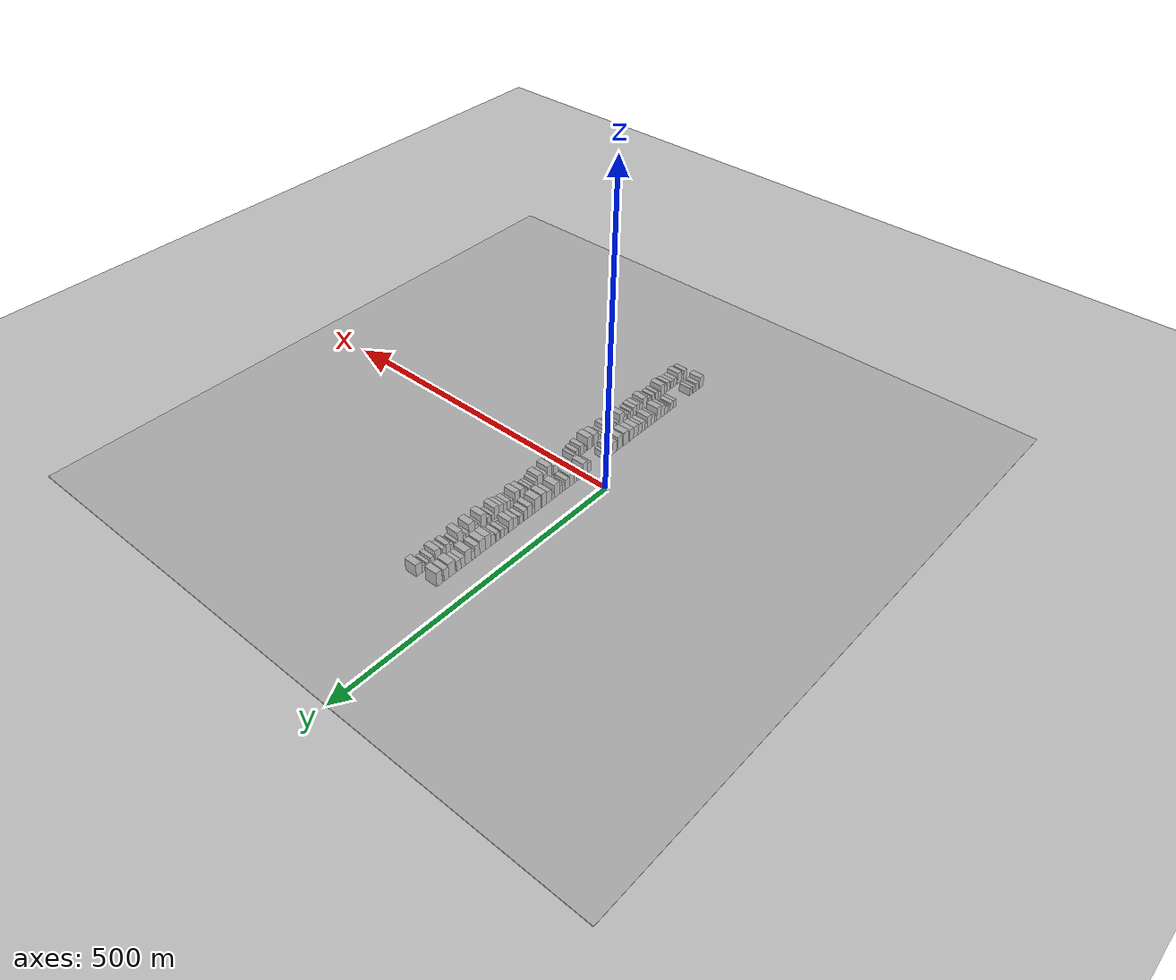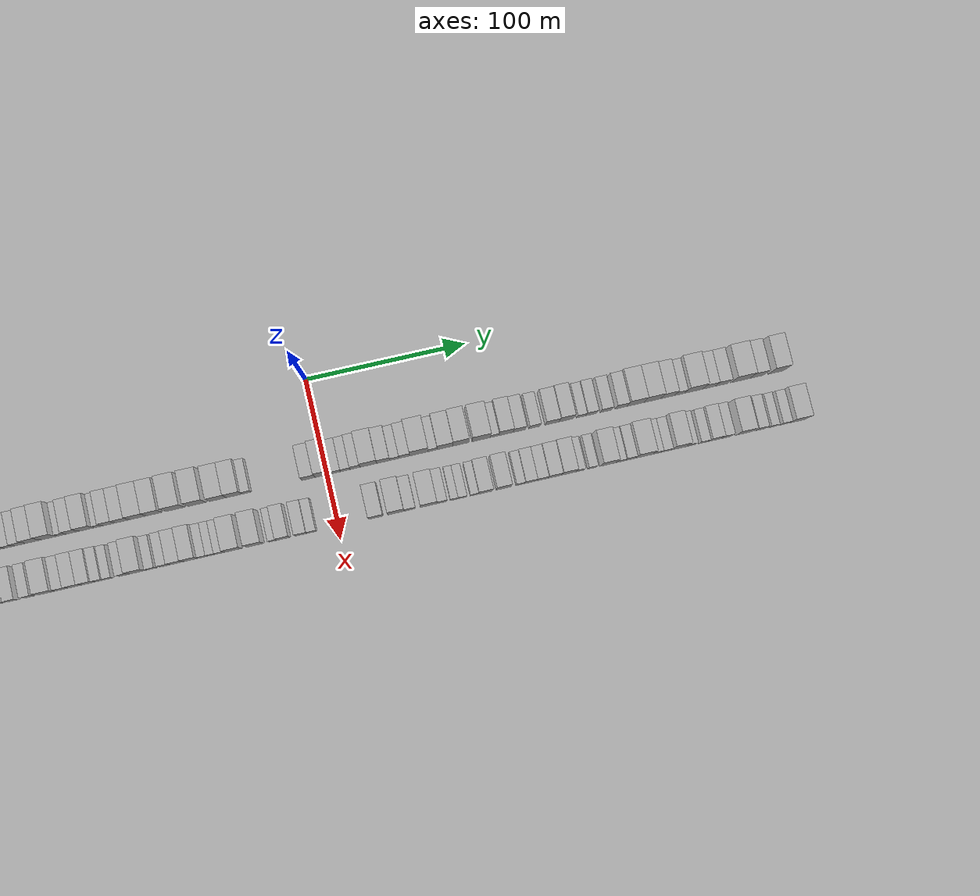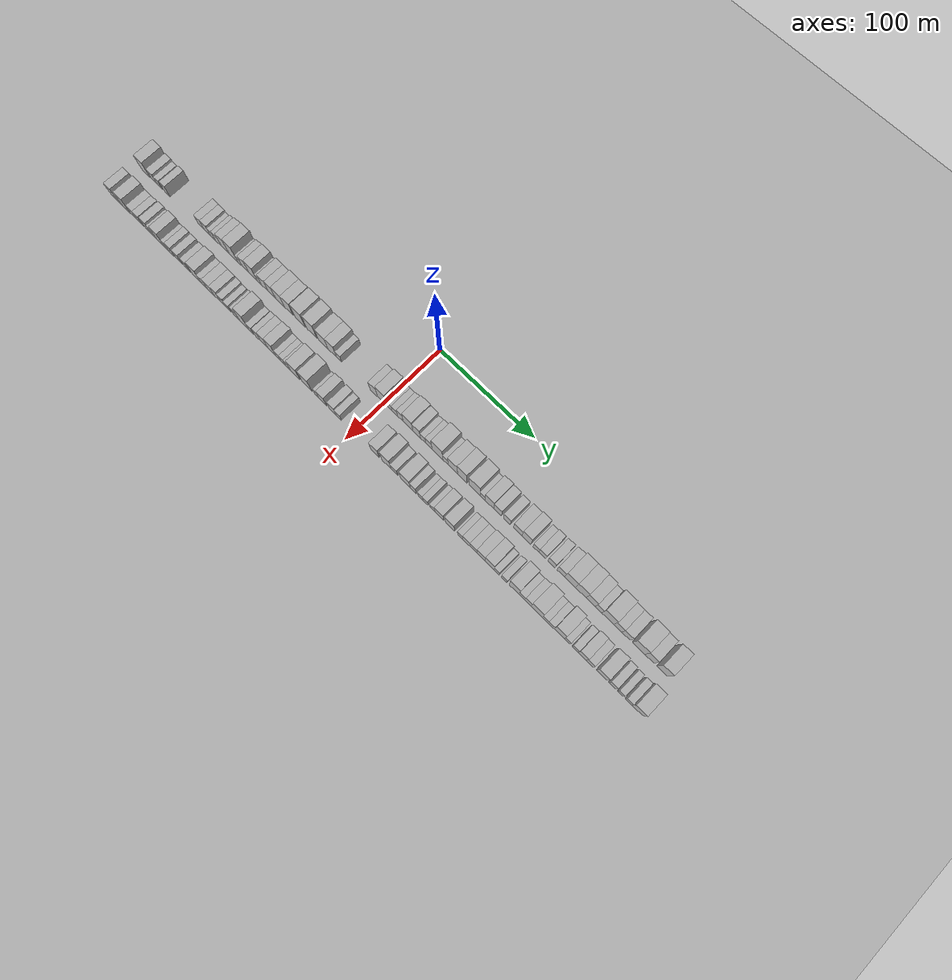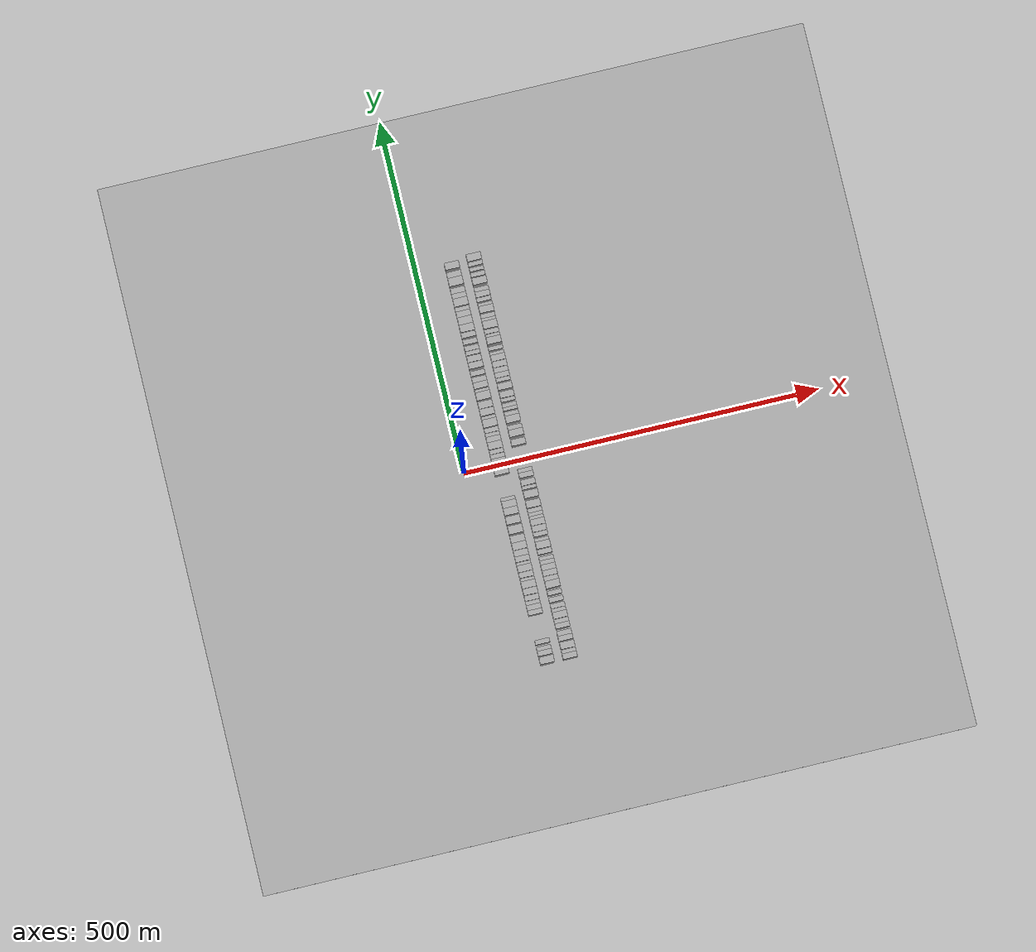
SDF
<?xml version="1.0" encoding="utf-8"?>

<sdf version="1.6">

   <world name="default">

      <gui fullscreen="0">

         <camera name="user_camera">

            <pose>-15 0 4.57585 0 0 0</pose>

            <view_controller>orbit</view_controller>

         </camera>

      </gui>

      <scene>

         <sky>

           <clouds>

             <speed>12</speed>

           </clouds>

         </sky>

         <ambient>0.4 0.4 0.4 1</ambient>

         <background>0.7 0.7 0.7 1</background>

         <shadows>1</shadows>

      </scene>

      <gravity>0 0 -9.8066</gravity>

      <magnetic_field>6e-06 2.3e-05 -4.2e-05</magnetic_field>

      <physics default="0" name="default_physics" type="ode">

         <ode>

            <solver>

               <type>quick</type>

               <iters>10</iters>

               <sor>1.0</sor>

               <use_dynamic_moi_rescaling>0</use_dynamic_moi_rescaling>

            </solver>

            <constraints>

               <cfm>0</cfm>

               <erp>0.2</erp>

               <contact_max_correcting_vel>100</contact_max_correcting_vel>

               <contact_surface_layer>0.001</contact_surface_layer>

            </constraints>

         </ode>

         <max_step_size>0.004</max_step_size>

         <real_time_factor>1</real_time_factor>

         <real_time_update_rate>250</real_time_update_rate>

      </physics>

      <light name="sun" type="directional">

         <cast_shadows>1</cast_shadows>

         <pose>0 0 10 0 0 0</pose>

         <diffuse>0.8 0.8 0.8 1</diffuse>

         <specular>0.2 0.2 0.2 1</specular>

         <attenuation>

            <range>1000</range>

            <constant>0.9</constant>

            <linear>0.01</linear>

            <quadratic>0.001</quadratic>

         </attenuation>

         <direction>-0.5 0.1 -0.9</direction>

      </light>

      <include>

         <name>ground_plane_1</name>

         <uri>model://HANNAS_ground_plane</uri>

         <pose>0 0 0  0 0 0</pose>

      </include>

      <include>

         <name>ground_plane_2</name>

         <uri>model://HANNAS_ground_plane</uri>

         <pose>100 0 0  0 0 0</pose>

      </include>

      <model name="building_1">

         <static>1</static>

         <pose frame="">50.0000 -276.9770 0 0.000000 0.000000 0.000000</pose>

         <link name="link">

            <pose frame="">0 0 10.50 0 0 0</pose>

            <collision name="collision">

               <geometry>

                  <box>

                     <size>20.0000 10.0460 21.0000</size>

                  </box>

               </geometry>

               <max_contacts>10</max_contacts>

               <surface>

                  <contact>

                     <ode/>

                  </contact>

                  <bounce/>

                  <friction>

                     <torsional>

                        <ode/>

                     </torsional>

                     <ode/>

                  </friction>

               </surface>

            </collision>

            <visual name="visual">

               <cast_shadows>0</cast_shadows>

               <geometry>

                  <box>

                     <size>20.0000 10.0460 21.0000</size>

                  </box>

               </geometry>

               <material>

                  <script>

                     <uri>model://HANNAS_wall/materials/scripts</uri>

                     <uri>model://HANNAS_wall/materials/textures</uri>

                     <name>vrc/HANNAS_wall</name>

                  </script>

               </material>

            </visual>

            <self_collide>0</self_collide>

            <enable_wind>0</enable_wind>

            <kinematic>0</kinematic>

         </link>

      </model>

      <model name="building_2">

         <static>1</static>

         <pose frame="">50.0000 -266.2607 0 0.000000 0.000000 0.000000</pose>

         <link name="link">

            <pose frame="">0 0 7.50 0 0 0</pose>

            <collision name="collision">

               <geometry>

                  <box>

                     <size>20.0000 7.3866 15.0000</size>

                  </box>

               </geometry>

               <max_contacts>10</max_contacts>

               <surface>

                  <contact>

                     <ode/>

                  </contact>

                  <bounce/>

                  <friction>

                     <torsional>

                        <ode/>

                     </torsional>

                     <ode/>

                  </friction>

               </surface>

            </collision>

            <visual name="visual">

               <cast_shadows>0</cast_shadows>

               <geometry>

                  <box>

                     <size>20.0000 7.3866 15.0000</size>

                  </box>

               </geometry>

               <material>

                  <script>

                     <uri>model://HANNAS_wall/materials/scripts</uri>

                     <uri>model://HANNAS_wall/materials/textures</uri>

                     <name>vrc/HANNAS_wall</name>

                  </script>

               </material>

            </visual>

            <self_collide>0</self_collide>

            <enable_wind>0</enable_wind>

            <kinematic>0</kinematic>

         </link>

      </model>

      <model name="building_3">

         <static>1</static>

         <pose frame="">50.0000 -259.7557 0 0.000000 0.000000 0.000000</pose>

         <link name="link">

            <pose frame="">0 0 6.00 0 0 0</pose>

            <collision name="collision">

               <geometry>

                  <box>

                     <size>20.0000 5.6234 12.0000</size>

                  </box>

               </geometry>

               <max_contacts>10</max_contacts>

               <surface>

                  <contact>

                     <ode/>

                  </contact>

                  <bounce/>

                  <friction>

                     <torsional>

                        <ode/>

                     </torsional>

                     <ode/>

                  </friction>

               </surface>

            </collision>

            <visual name="visual">

               <cast_shadows>0</cast_shadows>

               <geometry>

                  <box>

                     <size>20.0000 5.6234 12.0000</size>

                  </box>

               </geometry>

               <material>

                  <script>

                     <uri>model://HANNAS_wall/materials/scripts</uri>

                     <uri>model://HANNAS_wall/materials/textures</uri>

                     <name>vrc/HANNAS_wall</name>

                  </script>

               </material>

            </visual>

            <self_collide>0</self_collide>

            <enable_wind>0</enable_wind>

            <kinematic>0</kinematic>

         </link>

      </model>

      <model name="building_4">

         <static>1</static>

         <pose frame="">50.0000 -250.7331 0 0.000000 0.000000 0.000000</pose>

         <link name="link">

            <pose frame="">0 0 7.50 0 0 0</pose>

            <collision name="collision">

               <geometry>

                  <box>

                     <size>20.0000 6.4219 15.0000</size>

                  </box>

               </geometry>

               <max_contacts>10</max_contacts>

               <surface>

                  <contact>

                     <ode/>

                  </contact>

                  <bounce/>

                  <friction>

                     <torsional>

                        <ode/>

                     </torsional>

                     <ode/>

                  </friction>

               </surface>

            </collision>

            <visual name="visual">

               <cast_shadows>0</cast_shadows>

               <geometry>

                  <box>

                     <size>20.0000 6.4219 15.0000</size>

                  </box>

               </geometry>

               <material>

                  <script>

                     <uri>model://HANNAS_wall/materials/scripts</uri>

                     <uri>model://HANNAS_wall/materials/textures</uri>

                     <name>vrc/HANNAS_wall</name>

                  </script>

               </material>

            </visual>

            <self_collide>0</self_collide>

            <enable_wind>0</enable_wind>

            <kinematic>0</kinematic>

         </link>

      </model>

      <model name="building_5">

         <static>1</static>

         <pose frame="">50.0000 -209.0870 0 0.000000 0.000000 0.000000</pose>

         <link name="link">

            <pose frame="">0 0 7.50 0 0 0</pose>

            <collision name="collision">

               <geometry>

                  <box>

                     <size>20.0000 6.9568 15.0000</size>

                  </box>

               </geometry>

               <max_contacts>10</max_contacts>

               <surface>

                  <contact>

                     <ode/>

                  </contact>

                  <bounce/>

                  <friction>

                     <torsional>

                        <ode/>

                     </torsional>

                     <ode/>

                  </friction>

               </surface>

            </collision>

            <visual name="visual">

               <cast_shadows>0</cast_shadows>

               <geometry>

                  <box>

                     <size>20.0000 6.9568 15.0000</size>

                  </box>

               </geometry>

               <material>

                  <script>

                     <uri>model://HANNAS_wall/materials/scripts</uri>

                     <uri>model://HANNAS_wall/materials/textures</uri>

                     <name>vrc/HANNAS_wall</name>

                  </script>

               </material>

            </visual>

            <self_collide>0</self_collide>

            <enable_wind>0</enable_wind>

            <kinematic>0</kinematic>

         </link>

      </model>

      <model name="building_6">

         <static>1</static>

         <pose frame="">50.0000 -201.9308 0 0.000000 0.000000 0.000000</pose>

         <link name="link">

            <pose frame="">0 0 7.50 0 0 0</pose>

            <collision name="collision">

               <geometry>

                  <box>

                     <size>20.0000 7.3556 15.0000</size>

                  </box>

               </geometry>

               <max_contacts>10</max_contacts>

               <surface>

                  <contact>

                     <ode/>

                  </contact>

                  <bounce/>

                  <friction>

                     <torsional>

                        <ode/>

                     </torsional>

                     <ode/>

                  </friction>

               </surface>

            </collision>

            <visual name="visual">

               <cast_shadows>0</cast_shadows>

               <geometry>

                  <box>

                     <size>20.0000 7.3556 15.0000</size>

                  </box>

               </geometry>

               <material>

                  <script>

                     <uri>model://HANNAS_wall/materials/scripts</uri>

                     <uri>model://HANNAS_wall/materials/textures</uri>

                     <name>vrc/HANNAS_wall</name>

                  </script>

               </material>

            </visual>

            <self_collide>0</self_collide>

            <enable_wind>0</enable_wind>

            <kinematic>0</kinematic>

         </link>

      </model>

      <model name="building_7">

         <static>1</static>

         <pose frame="">50.0000 -195.3391 0 0.000000 0.000000 0.000000</pose>

         <link name="link">

            <pose frame="">0 0 6.00 0 0 0</pose>

            <collision name="collision">

               <geometry>

                  <box>

                     <size>20.0000 5.8279 12.0000</size>

                  </box>

               </geometry>

               <max_contacts>10</max_contacts>

               <surface>

                  <contact>

                     <ode/>

                  </contact>

                  <bounce/>

                  <friction>

                     <torsional>

                        <ode/>

                     </torsional>

                     <ode/>

                  </friction>

               </surface>

            </collision>

            <visual name="visual">

               <cast_shadows>0</cast_shadows>

               <geometry>

                  <box>

                     <size>20.0000 5.8279 12.0000</size>

                  </box>

               </geometry>

               <material>

                  <script>

                     <uri>model://HANNAS_wall/materials/scripts</uri>

                     <uri>model://HANNAS_wall/materials/textures</uri>

                     <name>vrc/HANNAS_wall</name>

                  </script>

               </material>

            </visual>

            <self_collide>0</self_collide>

            <enable_wind>0</enable_wind>

            <kinematic>0</kinematic>

         </link>

      </model>

      <model name="building_8">

         <static>1</static>

         <pose frame="">50.0000 -188.6798 0 0.000000 0.000000 0.000000</pose>

         <link name="link">

            <pose frame="">0 0 7.50 0 0 0</pose>

            <collision name="collision">

               <geometry>

                  <box>

                     <size>20.0000 7.4907 15.0000</size>

                  </box>

               </geometry>

               <max_contacts>10</max_contacts>

               <surface>

                  <contact>

                     <ode/>

                  </contact>

                  <bounce/>

                  <friction>

                     <torsional>

                        <ode/>

                     </torsional>

                     <ode/>

                  </friction>

               </surface>

            </collision>

            <visual name="visual">

               <cast_shadows>0</cast_shadows>

               <geometry>

                  <box>

                     <size>20.0000 7.4907 15.0000</size>

                  </box>

               </geometry>

               <material>

                  <script>

                     <uri>model://HANNAS_wall/materials/scripts</uri>

                     <uri>model://HANNAS_wall/materials/textures</uri>

                     <name>vrc/HANNAS_wall</name>

                  </script>

               </material>

            </visual>

            <self_collide>0</self_collide>

            <enable_wind>0</enable_wind>

            <kinematic>0</kinematic>

         </link>

      </model>

      <model name="building_9">

         <static>1</static>

         <pose frame="">50.0000 -180.3586 0 0.000000 0.000000 0.000000</pose>

         <link name="link">

            <pose frame="">0 0 10.50 0 0 0</pose>

            <collision name="collision">

               <geometry>

                  <box>

                     <size>20.0000 9.1517 21.0000</size>

                  </box>

               </geometry>

               <max_contacts>10</max_contacts>

               <surface>

                  <contact>

                     <ode/>

                  </contact>

                  <bounce/>

                  <friction>

                     <torsional>

                        <ode/>

                     </torsional>

                     <ode/>

                  </friction>

               </surface>

            </collision>

            <visual name="visual">

               <cast_shadows>0</cast_shadows>

               <geometry>

                  <box>

                     <size>20.0000 9.1517 21.0000</size>

                  </box>

               </geometry>

               <material>

                  <script>

                     <uri>model://HANNAS_wall/materials/scripts</uri>

                     <uri>model://HANNAS_wall/materials/textures</uri>

                     <name>vrc/HANNAS_wall</name>

                  </script>

               </material>

            </visual>

            <self_collide>0</self_collide>

            <enable_wind>0</enable_wind>

            <kinematic>0</kinematic>

         </link>

      </model>

      <model name="building_10">

         <static>1</static>

         <pose frame="">50.0000 -170.7274 0 0.000000 0.000000 0.000000</pose>

         <link name="link">

            <pose frame="">0 0 12.00 0 0 0</pose>

            <collision name="collision">

               <geometry>

                  <box>

                     <size>20.0000 10.1106 24.0000</size>

                  </box>

               </geometry>

               <max_contacts>10</max_contacts>

               <surface>

                  <contact>

                     <ode/>

                  </contact>

                  <bounce/>

                  <friction>

                     <torsional>

                        <ode/>

                     </torsional>

                     <ode/>

                  </friction>

               </surface>

            </collision>

            <visual name="visual">

               <cast_shadows>0</cast_shadows>

               <geometry>

                  <box>

                     <size>20.0000 10.1106 24.0000</size>

                  </box>

               </geometry>

               <material>

                  <script>

                     <uri>model://HANNAS_wall/materials/scripts</uri>

                     <uri>model://HANNAS_wall/materials/textures</uri>

                     <name>vrc/HANNAS_wall</name>

                  </script>

               </material>

            </visual>

            <self_collide>0</self_collide>

            <enable_wind>0</enable_wind>

            <kinematic>0</kinematic>

         </link>

      </model>

      <model name="building_11">

         <static>1</static>

         <pose frame="">50.0000 -163.0264 0 0.000000 0.000000 0.000000</pose>

         <link name="link">

            <pose frame="">0 0 6.00 0 0 0</pose>

            <collision name="collision">

               <geometry>

                  <box>

                     <size>20.0000 5.2915 12.0000</size>

                  </box>

               </geometry>

               <max_contacts>10</max_contacts>

               <surface>

                  <contact>

                     <ode/>

                  </contact>

                  <bounce/>

                  <friction>

                     <torsional>

                        <ode/>

                     </torsional>

                     <ode/>

                  </friction>

               </surface>

            </collision>

            <visual name="visual">

               <cast_shadows>0</cast_shadows>

               <geometry>

                  <box>

                     <size>20.0000 5.2915 12.0000</size>

                  </box>

               </geometry>

               <material>

                  <script>

                     <uri>model://HANNAS_wall/materials/scripts</uri>

                     <uri>model://HANNAS_wall/materials/textures</uri>

                     <name>vrc/HANNAS_wall</name>

                  </script>

               </material>

            </visual>

            <self_collide>0</self_collide>

            <enable_wind>0</enable_wind>

            <kinematic>0</kinematic>

         </link>

      </model>

      <model name="building_12">

         <static>1</static>

         <pose frame="">50.0000 -156.4857 0 0.000000 0.000000 0.000000</pose>

         <link name="link">

            <pose frame="">0 0 9.00 0 0 0</pose>

            <collision name="collision">

               <geometry>

                  <box>

                     <size>20.0000 7.7898 18.0000</size>

                  </box>

               </geometry>

               <max_contacts>10</max_contacts>

               <surface>

                  <contact>

                     <ode/>

                  </contact>

                  <bounce/>

                  <friction>

                     <torsional>

                        <ode/>

                     </torsional>

                     <ode/>

                  </friction>

               </surface>

            </collision>

            <visual name="visual">

               <cast_shadows>0</cast_shadows>

               <geometry>

                  <box>

                     <size>20.0000 7.7898 18.0000</size>

                  </box>

               </geometry>

               <material>

                  <script>

                     <uri>model://HANNAS_wall/materials/scripts</uri>

                     <uri>model://HANNAS_wall/materials/textures</uri>

                     <name>vrc/HANNAS_wall</name>

                  </script>

               </material>

            </visual>

            <self_collide>0</self_collide>

            <enable_wind>0</enable_wind>

            <kinematic>0</kinematic>

         </link>

      </model>

      <model name="building_13">

         <static>1</static>

         <pose frame="">50.0000 -147.7321 0 0.000000 0.000000 0.000000</pose>

         <link name="link">

            <pose frame="">0 0 10.50 0 0 0</pose>

            <collision name="collision">

               <geometry>

                  <box>

                     <size>20.0000 9.7174 21.0000</size>

                  </box>

               </geometry>

               <max_contacts>10</max_contacts>

               <surface>

                  <contact>

                     <ode/>

                  </contact>

                  <bounce/>

                  <friction>

                     <torsional>

                        <ode/>

                     </torsional>

                     <ode/>

                  </friction>

               </surface>

            </collision>

            <visual name="visual">

               <cast_shadows>0</cast_shadows>

               <geometry>

                  <box>

                     <size>20.0000 9.7174 21.0000</size>

                  </box>

               </geometry>

               <material>

                  <script>

                     <uri>model://HANNAS_wall/materials/scripts</uri>

                     <uri>model://HANNAS_wall/materials/textures</uri>

                     <name>vrc/HANNAS_wall</name>

                  </script>

               </material>

            </visual>

            <self_collide>0</self_collide>

            <enable_wind>0</enable_wind>

            <kinematic>0</kinematic>

         </link>

      </model>

      <model name="building_14">

         <static>1</static>

         <pose frame="">50.0000 -140.4403 0 0.000000 0.000000 0.000000</pose>

         <link name="link">

            <pose frame="">0 0 6.00 0 0 0</pose>

            <collision name="collision">

               <geometry>

                  <box>

                     <size>20.0000 4.8661 12.0000</size>

                  </box>

               </geometry>

               <max_contacts>10</max_contacts>

               <surface>

                  <contact>

                     <ode/>

                  </contact>

                  <bounce/>

                  <friction>

                     <torsional>

                        <ode/>

                     </torsional>

                     <ode/>

                  </friction>

               </surface>

            </collision>

            <visual name="visual">

               <cast_shadows>0</cast_shadows>

               <geometry>

                  <box>

                     <size>20.0000 4.8661 12.0000</size>

                  </box>

               </geometry>

               <material>

                  <script>

                     <uri>model://HANNAS_wall/materials/scripts</uri>

                     <uri>model://HANNAS_wall/materials/textures</uri>

                     <name>vrc/HANNAS_wall</name>

                  </script>

               </material>

            </visual>

            <self_collide>0</self_collide>

            <enable_wind>0</enable_wind>

            <kinematic>0</kinematic>

         </link>

      </model>

      <model name="building_15">

         <static>1</static>

         <pose frame="">50.0000 -134.0375 0 0.000000 0.000000 0.000000</pose>

         <link name="link">

            <pose frame="">0 0 9.00 0 0 0</pose>

            <collision name="collision">

               <geometry>

                  <box>

                     <size>20.0000 7.9396 18.0000</size>

                  </box>

               </geometry>

               <max_contacts>10</max_contacts>

               <surface>

                  <contact>

                     <ode/>

                  </contact>

                  <bounce/>

                  <friction>

                     <torsional>

                        <ode/>

                     </torsional>

                     <ode/>

                  </friction>

               </surface>

            </collision>

            <visual name="visual">

               <cast_shadows>0</cast_shadows>

               <geometry>

                  <box>

                     <size>20.0000 7.9396 18.0000</size>

                  </box>

               </geometry>

               <material>

                  <script>

                     <uri>model://HANNAS_wall/materials/scripts</uri>

                     <uri>model://HANNAS_wall/materials/textures</uri>

                     <name>vrc/HANNAS_wall</name>

                  </script>

               </material>

            </visual>

            <self_collide>0</self_collide>

            <enable_wind>0</enable_wind>

            <kinematic>0</kinematic>

         </link>

      </model>

      <model name="building_16">

         <static>1</static>

         <pose frame="">50.0000 -125.7785 0 0.000000 0.000000 0.000000</pose>

         <link name="link">

            <pose frame="">0 0 9.00 0 0 0</pose>

            <collision name="collision">

               <geometry>

                  <box>

                     <size>20.0000 8.5782 18.0000</size>

                  </box>

               </geometry>

               <max_contacts>10</max_contacts>

               <surface>

                  <contact>

                     <ode/>

                  </contact>

                  <bounce/>

                  <friction>

                     <torsional>

                        <ode/>

                     </torsional>

                     <ode/>

                  </friction>

               </surface>

            </collision>

            <visual name="visual">

               <cast_shadows>0</cast_shadows>

               <geometry>

                  <box>

                     <size>20.0000 8.5782 18.0000</size>

                  </box>

               </geometry>

               <material>

                  <script>

                     <uri>model://HANNAS_wall/materials/scripts</uri>

                     <uri>model://HANNAS_wall/materials/textures</uri>

                     <name>vrc/HANNAS_wall</name>

                  </script>

               </material>

            </visual>

            <self_collide>0</self_collide>

            <enable_wind>0</enable_wind>

            <kinematic>0</kinematic>

         </link>

      </model>

      <model name="building_17">

         <static>1</static>

         <pose frame="">50.0000 -116.2439 0 0.000000 0.000000 0.000000</pose>

         <link name="link">

            <pose frame="">0 0 10.50 0 0 0</pose>

            <collision name="collision">

               <geometry>

                  <box>

                     <size>20.0000 10.4910 21.0000</size>

                  </box>

               </geometry>

               <max_contacts>10</max_contacts>

               <surface>

                  <contact>

                     <ode/>

                  </contact>

                  <bounce/>

                  <friction>

                     <torsional>

                        <ode/>

                     </torsional>

                     <ode/>

                  </friction>

               </surface>

            </collision>

            <visual name="visual">

               <cast_shadows>0</cast_shadows>

               <geometry>

                  <box>

                     <size>20.0000 10.4910 21.0000</size>

                  </box>

               </geometry>

               <material>

                  <script>

                     <uri>model://HANNAS_wall/materials/scripts</uri>

                     <uri>model://HANNAS_wall/materials/textures</uri>

                     <name>vrc/HANNAS_wall</name>

                  </script>

               </material>

            </visual>

            <self_collide>0</self_collide>

            <enable_wind>0</enable_wind>

            <kinematic>0</kinematic>

         </link>

      </model>

      <model name="building_18">

         <static>1</static>

         <pose frame="">50.0000 -106.0777 0 0.000000 0.000000 0.000000</pose>

         <link name="link">

            <pose frame="">0 0 10.50 0 0 0</pose>

            <collision name="collision">

               <geometry>

                  <box>

                     <size>20.0000 9.8415 21.0000</size>

                  </box>

               </geometry>

               <max_contacts>10</max_contacts>

               <surface>

                  <contact>

                     <ode/>

                  </contact>

                  <bounce/>

                  <friction>

                     <torsional>

                        <ode/>

                     </torsional>

                     <ode/>

                  </friction>

               </surface>

            </collision>

            <visual name="visual">

               <cast_shadows>0</cast_shadows>

               <geometry>

                  <box>

                     <size>20.0000 9.8415 21.0000</size>

                  </box>

               </geometry>

               <material>

                  <script>

                     <uri>model://HANNAS_wall/materials/scripts</uri>

                     <uri>model://HANNAS_wall/materials/textures</uri>

                     <name>vrc/HANNAS_wall</name>

                  </script>

               </material>

            </visual>

            <self_collide>0</self_collide>

            <enable_wind>0</enable_wind>

            <kinematic>0</kinematic>

         </link>

      </model>

      <model name="building_19">

         <static>1</static>

         <pose frame="">50.0000 -93.3083 0 0.000000 0.000000 0.000000</pose>

         <link name="link">

            <pose frame="">0 0 12.00 0 0 0</pose>

            <collision name="collision">

               <geometry>

                  <box>

                     <size>20.0000 11.6972 24.0000</size>

                  </box>

               </geometry>

               <max_contacts>10</max_contacts>

               <surface>

                  <contact>

                     <ode/>

                  </contact>

                  <bounce/>

                  <friction>

                     <torsional>

                        <ode/>

                     </torsional>

                     <ode/>

                  </friction>

               </surface>

            </collision>

            <visual name="visual">

               <cast_shadows>0</cast_shadows>

               <geometry>

                  <box>

                     <size>20.0000 11.6972 24.0000</size>

                  </box>

               </geometry>

               <material>

                  <script>

                     <uri>model://HANNAS_wall/materials/scripts</uri>

                     <uri>model://HANNAS_wall/materials/textures</uri>

                     <name>vrc/HANNAS_wall</name>

                  </script>

               </material>

            </visual>

            <self_collide>0</self_collide>

            <enable_wind>0</enable_wind>

            <kinematic>0</kinematic>

         </link>

      </model>

      <model name="building_20">

         <static>1</static>

         <pose frame="">50.0000 -79.8565 0 0.000000 0.000000 0.000000</pose>

         <link name="link">

            <pose frame="">0 0 12.00 0 0 0</pose>

            <collision name="collision">

               <geometry>

                  <box>

                     <size>20.0000 11.2065 24.0000</size>

                  </box>

               </geometry>

               <max_contacts>10</max_contacts>

               <surface>

                  <contact>

                     <ode/>

                  </contact>

                  <bounce/>

                  <friction>

                     <torsional>

                        <ode/>

                     </torsional>

                     <ode/>

                  </friction>

               </surface>

            </collision>

            <visual name="visual">

               <cast_shadows>0</cast_shadows>

               <geometry>

                  <box>

                     <size>20.0000 11.2065 24.0000</size>

                  </box>

               </geometry>

               <material>

                  <script>

                     <uri>model://HANNAS_wall/materials/scripts</uri>

                     <uri>model://HANNAS_wall/materials/textures</uri>

                     <name>vrc/HANNAS_wall</name>

                  </script>

               </material>

            </visual>

            <self_collide>0</self_collide>

            <enable_wind>0</enable_wind>

            <kinematic>0</kinematic>

         </link>

      </model>

      <model name="building_21">

         <static>1</static>

         <pose frame="">50.0000 -67.0603 0 0.000000 0.000000 0.000000</pose>

         <link name="link">

            <pose frame="">0 0 10.50 0 0 0</pose>

            <collision name="collision">

               <geometry>

                  <box>

                     <size>20.0000 10.3857 21.0000</size>

                  </box>

               </geometry>

               <max_contacts>10</max_contacts>

               <surface>

                  <contact>

                     <ode/>

                  </contact>

                  <bounce/>

                  <friction>

                     <torsional>

                        <ode/>

                     </torsional>

                     <ode/>

                  </friction>

               </surface>

            </collision>

            <visual name="visual">

               <cast_shadows>0</cast_shadows>

               <geometry>

                  <box>

                     <size>20.0000 10.3857 21.0000</size>

                  </box>

               </geometry>

               <material>

                  <script>

                     <uri>model://HANNAS_wall/materials/scripts</uri>

                     <uri>model://HANNAS_wall/materials/textures</uri>

                     <name>vrc/HANNAS_wall</name>

                  </script>

               </material>

            </visual>

            <self_collide>0</self_collide>

            <enable_wind>0</enable_wind>

            <kinematic>0</kinematic>

         </link>

      </model>

      <model name="building_22">

         <static>1</static>

         <pose frame="">50.0000 -57.0020 0 0.000000 0.000000 0.000000</pose>

         <link name="link">

            <pose frame="">0 0 10.50 0 0 0</pose>

            <collision name="collision">

               <geometry>

                  <box>

                     <size>20.0000 9.7309 21.0000</size>

                  </box>

               </geometry>

               <max_contacts>10</max_contacts>

               <surface>

                  <contact>

                     <ode/>

                  </contact>

                  <bounce/>

                  <friction>

                     <torsional>

                        <ode/>

                     </torsional>

                     <ode/>

                  </friction>

               </surface>

            </collision>

            <visual name="visual">

               <cast_shadows>0</cast_shadows>

               <geometry>

                  <box>

                     <size>20.0000 9.7309 21.0000</size>

                  </box>

               </geometry>

               <material>

                  <script>

                     <uri>model://HANNAS_wall/materials/scripts</uri>

                     <uri>model://HANNAS_wall/materials/textures</uri>

                     <name>vrc/HANNAS_wall</name>

                  </script>

               </material>

            </visual>

            <self_collide>0</self_collide>

            <enable_wind>0</enable_wind>

            <kinematic>0</kinematic>

         </link>

      </model>

      <model name="building_23">

         <static>1</static>

         <pose frame="">50.0000 -49.3145 0 0.000000 0.000000 0.000000</pose>

         <link name="link">

            <pose frame="">0 0 6.00 0 0 0</pose>

            <collision name="collision">

               <geometry>

                  <box>

                     <size>20.0000 5.6441 12.0000</size>

                  </box>

               </geometry>

               <max_contacts>10</max_contacts>

               <surface>

                  <contact>

                     <ode/>

                  </contact>

                  <bounce/>

                  <friction>

                     <torsional>

                        <ode/>

                     </torsional>

                     <ode/>

                  </friction>

               </surface>

            </collision>

            <visual name="visual">

               <cast_shadows>0</cast_shadows>

               <geometry>

                  <box>

                     <size>20.0000 5.6441 12.0000</size>

                  </box>

               </geometry>

               <material>

                  <script>

                     <uri>model://HANNAS_wall/materials/scripts</uri>

                     <uri>model://HANNAS_wall/materials/textures</uri>

                     <name>vrc/HANNAS_wall</name>

                  </script>

               </material>

            </visual>

            <self_collide>0</self_collide>

            <enable_wind>0</enable_wind>

            <kinematic>0</kinematic>

         </link>

      </model>

      <model name="building_24">

         <static>1</static>

         <pose frame="">50.0000 -11.0060 0 0.000000 0.000000 0.000000</pose>

         <link name="link">

            <pose frame="">0 0 9.00 0 0 0</pose>

            <collision name="collision">

               <geometry>

                  <box>

                     <size>20.0000 8.3243 18.0000</size>

                  </box>

               </geometry>

               <max_contacts>10</max_contacts>

               <surface>

                  <contact>

                     <ode/>

                  </contact>

                  <bounce/>

                  <friction>

                     <torsional>

                        <ode/>

                     </torsional>

                     <ode/>

                  </friction>

               </surface>

            </collision>

            <visual name="visual">

               <cast_shadows>0</cast_shadows>

               <geometry>

                  <box>

                     <size>20.0000 8.3243 18.0000</size>

                  </box>

               </geometry>

               <material>

                  <script>

                     <uri>model://HANNAS_wall/materials/scripts</uri>

                     <uri>model://HANNAS_wall/materials/textures</uri>

                     <name>vrc/HANNAS_wall</name>

                  </script>

               </material>

            </visual>

            <self_collide>0</self_collide>

            <enable_wind>0</enable_wind>

            <kinematic>0</kinematic>

         </link>

      </model>

      <model name="building_25">

         <static>1</static>

         <pose frame="">50.0000 -1.9541 0 0.000000 0.000000 0.000000</pose>

         <link name="link">

            <pose frame="">0 0 12.00 0 0 0</pose>

            <collision name="collision">

               <geometry>

                  <box>

                     <size>20.0000 9.7796 24.0000</size>

                  </box>

               </geometry>

               <max_contacts>10</max_contacts>

               <surface>

                  <contact>

                     <ode/>

                  </contact>

                  <bounce/>

                  <friction>

                     <torsional>

                        <ode/>

                     </torsional>

                     <ode/>

                  </friction>

               </surface>

            </collision>

            <visual name="visual">

               <cast_shadows>0</cast_shadows>

               <geometry>

                  <box>

                     <size>20.0000 9.7796 24.0000</size>

                  </box>

               </geometry>

               <material>

                  <script>

                     <uri>model://HANNAS_wall/materials/scripts</uri>

                     <uri>model://HANNAS_wall/materials/textures</uri>

                     <name>vrc/HANNAS_wall</name>

                  </script>

               </material>

            </visual>

            <self_collide>0</self_collide>

            <enable_wind>0</enable_wind>

            <kinematic>0</kinematic>

         </link>

      </model>

      <model name="building_26">

         <static>1</static>

         <pose frame="">50.0000 5.8931 0 0.000000 0.000000 0.000000</pose>

         <link name="link">

            <pose frame="">0 0 6.00 0 0 0</pose>

            <collision name="collision">

               <geometry>

                  <box>

                     <size>20.0000 5.9147 12.0000</size>

                  </box>

               </geometry>

               <max_contacts>10</max_contacts>

               <surface>

                  <contact>

                     <ode/>

                  </contact>

                  <bounce/>

                  <friction>

                     <torsional>

                        <ode/>

                     </torsional>

                     <ode/>

                  </friction>

               </surface>

            </collision>

            <visual name="visual">

               <cast_shadows>0</cast_shadows>

               <geometry>

                  <box>

                     <size>20.0000 5.9147 12.0000</size>

                  </box>

               </geometry>

               <material>

                  <script>

                     <uri>model://HANNAS_wall/materials/scripts</uri>

                     <uri>model://HANNAS_wall/materials/textures</uri>

                     <name>vrc/HANNAS_wall</name>

                  </script>

               </material>

            </visual>

            <self_collide>0</self_collide>

            <enable_wind>0</enable_wind>

            <kinematic>0</kinematic>

         </link>

      </model>

      <model name="building_27">

         <static>1</static>

         <pose frame="">50.0000 11.8001 0 0.000000 0.000000 0.000000</pose>

         <link name="link">

            <pose frame="">0 0 6.00 0 0 0</pose>

            <collision name="collision">

               <geometry>

                  <box>

                     <size>20.0000 5.8994 12.0000</size>

                  </box>

               </geometry>

               <max_contacts>10</max_contacts>

               <surface>

                  <contact>

                     <ode/>

                  </contact>

                  <bounce/>

                  <friction>

                     <torsional>

                        <ode/>

                     </torsional>

                     <ode/>

                  </friction>

               </surface>

            </collision>

            <visual name="visual">

               <cast_shadows>0</cast_shadows>

               <geometry>

                  <box>

                     <size>20.0000 5.8994 12.0000</size>

                  </box>

               </geometry>

               <material>

                  <script>

                     <uri>model://HANNAS_wall/materials/scripts</uri>

                     <uri>model://HANNAS_wall/materials/textures</uri>

                     <name>vrc/HANNAS_wall</name>

                  </script>

               </material>

            </visual>

            <self_collide>0</self_collide>

            <enable_wind>0</enable_wind>

            <kinematic>0</kinematic>

         </link>

      </model>

      <model name="building_28">

         <static>1</static>

         <pose frame="">50.0000 17.8143 0 0.000000 0.000000 0.000000</pose>

         <link name="link">

            <pose frame="">0 0 7.50 0 0 0</pose>

            <collision name="collision">

               <geometry>

                  <box>

                     <size>20.0000 6.1291 15.0000</size>

                  </box>

               </geometry>

               <max_contacts>10</max_contacts>

               <surface>

                  <contact>

                     <ode/>

                  </contact>

                  <bounce/>

                  <friction>

                     <torsional>

                        <ode/>

                     </torsional>

                     <ode/>

                  </friction>

               </surface>

            </collision>

            <visual name="visual">

               <cast_shadows>0</cast_shadows>

               <geometry>

                  <box>

                     <size>20.0000 6.1291 15.0000</size>

                  </box>

               </geometry>

               <material>

                  <script>

                     <uri>model://HANNAS_wall/materials/scripts</uri>

                     <uri>model://HANNAS_wall/materials/textures</uri>

                     <name>vrc/HANNAS_wall</name>

                  </script>

               </material>

            </visual>

            <self_collide>0</self_collide>

            <enable_wind>0</enable_wind>

            <kinematic>0</kinematic>

         </link>

      </model>

      <model name="building_29">

         <static>1</static>

         <pose frame="">50.0000 26.0660 0 0.000000 0.000000 0.000000</pose>

         <link name="link">

            <pose frame="">0 0 10.50 0 0 0</pose>

            <collision name="collision">

               <geometry>

                  <box>

                     <size>20.0000 10.3743 21.0000</size>

                  </box>

               </geometry>

               <max_contacts>10</max_contacts>

               <surface>

                  <contact>

                     <ode/>

                  </contact>

                  <bounce/>

                  <friction>

                     <torsional>

                        <ode/>

                     </torsional>

                     <ode/>

                  </friction>

               </surface>

            </collision>

            <visual name="visual">

               <cast_shadows>0</cast_shadows>

               <geometry>

                  <box>

                     <size>20.0000 10.3743 21.0000</size>

                  </box>

               </geometry>

               <material>

                  <script>

                     <uri>model://HANNAS_wall/materials/scripts</uri>

                     <uri>model://HANNAS_wall/materials/textures</uri>

                     <name>vrc/HANNAS_wall</name>

                  </script>

               </material>

            </visual>

            <self_collide>0</self_collide>

            <enable_wind>0</enable_wind>

            <kinematic>0</kinematic>

         </link>

      </model>

      <model name="building_30">

         <static>1</static>

         <pose frame="">50.0000 35.2539 0 0.000000 0.000000 0.000000</pose>

         <link name="link">

            <pose frame="">0 0 9.00 0 0 0</pose>

            <collision name="collision">

               <geometry>

                  <box>

                     <size>20.0000 8.0016 18.0000</size>

                  </box>

               </geometry>

               <max_contacts>10</max_contacts>

               <surface>

                  <contact>

                     <ode/>

                  </contact>

                  <bounce/>

                  <friction>

                     <torsional>

                        <ode/>

                     </torsional>

                     <ode/>

                  </friction>

               </surface>

            </collision>

            <visual name="visual">

               <cast_shadows>0</cast_shadows>

               <geometry>

                  <box>

                     <size>20.0000 8.0016 18.0000</size>

                  </box>

               </geometry>

               <material>

                  <script>

                     <uri>model://HANNAS_wall/materials/scripts</uri>

                     <uri>model://HANNAS_wall/materials/textures</uri>

                     <name>vrc/HANNAS_wall</name>

                  </script>

               </material>

            </visual>

            <self_collide>0</self_collide>

            <enable_wind>0</enable_wind>

            <kinematic>0</kinematic>

         </link>

      </model>

      <model name="building_31">

         <static>1</static>

         <pose frame="">50.0000 42.0999 0 0.000000 0.000000 0.000000</pose>

         <link name="link">

            <pose frame="">0 0 6.00 0 0 0</pose>

            <collision name="collision">

               <geometry>

                  <box>

                     <size>20.0000 5.6902 12.0000</size>

                  </box>

               </geometry>

               <max_contacts>10</max_contacts>

               <surface>

                  <contact>

                     <ode/>

                  </contact>

                  <bounce/>

                  <friction>

                     <torsional>

                        <ode/>

                     </torsional>

                     <ode/>

                  </friction>

               </surface>

            </collision>

            <visual name="visual">

               <cast_shadows>0</cast_shadows>

               <geometry>

                  <box>

                     <size>20.0000 5.6902 12.0000</size>

                  </box>

               </geometry>

               <material>

                  <script>

                     <uri>model://HANNAS_wall/materials/scripts</uri>

                     <uri>model://HANNAS_wall/materials/textures</uri>

                     <name>vrc/HANNAS_wall</name>

                  </script>

               </material>

            </visual>

            <self_collide>0</self_collide>

            <enable_wind>0</enable_wind>

            <kinematic>0</kinematic>

         </link>

      </model>

      <model name="building_32">

         <static>1</static>

         <pose frame="">50.0000 48.2568 0 0.000000 0.000000 0.000000</pose>

         <link name="link">

            <pose frame="">0 0 7.50 0 0 0</pose>

            <collision name="collision">

               <geometry>

                  <box>

                     <size>20.0000 6.6237 15.0000</size>

                  </box>

               </geometry>

               <max_contacts>10</max_contacts>

               <surface>

                  <contact>

                     <ode/>

                  </contact>

                  <bounce/>

                  <friction>

                     <torsional>

                        <ode/>

                     </torsional>

                     <ode/>

                  </friction>

               </surface>

            </collision>

            <visual name="visual">

               <cast_shadows>0</cast_shadows>

               <geometry>

                  <box>

                     <size>20.0000 6.6237 15.0000</size>

                  </box>

               </geometry>

               <material>

                  <script>

                     <uri>model://HANNAS_wall/materials/scripts</uri>

                     <uri>model://HANNAS_wall/materials/textures</uri>

                     <name>vrc/HANNAS_wall</name>

                  </script>

               </material>

            </visual>

            <self_collide>0</self_collide>

            <enable_wind>0</enable_wind>

            <kinematic>0</kinematic>

         </link>

      </model>

      <model name="building_33">

         <static>1</static>

         <pose frame="">50.0000 57.3167 0 0.000000 0.000000 0.000000</pose>

         <link name="link">

            <pose frame="">0 0 12.00 0 0 0</pose>

            <collision name="collision">

               <geometry>

                  <box>

                     <size>20.0000 11.4961 24.0000</size>

                  </box>

               </geometry>

               <max_contacts>10</max_contacts>

               <surface>

                  <contact>

                     <ode/>

                  </contact>

                  <bounce/>

                  <friction>

                     <torsional>

                        <ode/>

                     </torsional>

                     <ode/>

                  </friction>

               </surface>

            </collision>

            <visual name="visual">

               <cast_shadows>0</cast_shadows>

               <geometry>

                  <box>

                     <size>20.0000 11.4961 24.0000</size>

                  </box>

               </geometry>

               <material>

                  <script>

                     <uri>model://HANNAS_wall/materials/scripts</uri>

                     <uri>model://HANNAS_wall/materials/textures</uri>

                     <name>vrc/HANNAS_wall</name>

                  </script>

               </material>

            </visual>

            <self_collide>0</self_collide>

            <enable_wind>0</enable_wind>

            <kinematic>0</kinematic>

         </link>

      </model>

      <model name="building_34">

         <static>1</static>

         <pose frame="">50.0000 65.8252 0 0.000000 0.000000 0.000000</pose>

         <link name="link">

            <pose frame="">0 0 6.00 0 0 0</pose>

            <collision name="collision">

               <geometry>

                  <box>

                     <size>20.0000 5.5210 12.0000</size>

                  </box>

               </geometry>

               <max_contacts>10</max_contacts>

               <surface>

                  <contact>

                     <ode/>

                  </contact>

                  <bounce/>

                  <friction>

                     <torsional>

                        <ode/>

                     </torsional>

                     <ode/>

                  </friction>

               </surface>

            </collision>

            <visual name="visual">

               <cast_shadows>0</cast_shadows>

               <geometry>

                  <box>

                     <size>20.0000 5.5210 12.0000</size>

                  </box>

               </geometry>

               <material>

                  <script>

                     <uri>model://HANNAS_wall/materials/scripts</uri>

                     <uri>model://HANNAS_wall/materials/textures</uri>

                     <name>vrc/HANNAS_wall</name>

                  </script>

               </material>

            </visual>

            <self_collide>0</self_collide>

            <enable_wind>0</enable_wind>

            <kinematic>0</kinematic>

         </link>

      </model>

      <model name="building_35">

         <static>1</static>

         <pose frame="">50.0000 73.5058 0 0.000000 0.000000 0.000000</pose>

         <link name="link">

            <pose frame="">0 0 10.50 0 0 0</pose>

            <collision name="collision">

               <geometry>

                  <box>

                     <size>20.0000 9.8404 21.0000</size>

                  </box>

               </geometry>

               <max_contacts>10</max_contacts>

               <surface>

                  <contact>

                     <ode/>

                  </contact>

                  <bounce/>

                  <friction>

                     <torsional>

                        <ode/>

                     </torsional>

                     <ode/>

                  </friction>

               </surface>

            </collision>

            <visual name="visual">

               <cast_shadows>0</cast_shadows>

               <geometry>

                  <box>

                     <size>20.0000 9.8404 21.0000</size>

                  </box>

               </geometry>

               <material>

                  <script>

                     <uri>model://HANNAS_wall/materials/scripts</uri>

                     <uri>model://HANNAS_wall/materials/textures</uri>

                     <name>vrc/HANNAS_wall</name>

                  </script>

               </material>

            </visual>

            <self_collide>0</self_collide>

            <enable_wind>0</enable_wind>

            <kinematic>0</kinematic>

         </link>

      </model>

      <model name="building_36">

         <static>1</static>

         <pose frame="">50.0000 83.3782 0 0.000000 0.000000 0.000000</pose>

         <link name="link">

            <pose frame="">0 0 12.00 0 0 0</pose>

            <collision name="collision">

               <geometry>

                  <box>

                     <size>20.0000 9.9043 24.0000</size>

                  </box>

               </geometry>

               <max_contacts>10</max_contacts>

               <surface>

                  <contact>

                     <ode/>

                  </contact>

                  <bounce/>

                  <friction>

                     <torsional>

                        <ode/>

                     </torsional>

                     <ode/>

                  </friction>

               </surface>

            </collision>

            <visual name="visual">

               <cast_shadows>0</cast_shadows>

               <geometry>

                  <box>

                     <size>20.0000 9.9043 24.0000</size>

                  </box>

               </geometry>

               <material>

                  <script>

                     <uri>model://HANNAS_wall/materials/scripts</uri>

                     <uri>model://HANNAS_wall/materials/textures</uri>

                     <name>vrc/HANNAS_wall</name>

                  </script>

               </material>

            </visual>

            <self_collide>0</self_collide>

            <enable_wind>0</enable_wind>

            <kinematic>0</kinematic>

         </link>

      </model>

      <model name="building_37">

         <static>1</static>

         <pose frame="">50.0000 96.0265 0 0.000000 0.000000 0.000000</pose>

         <link name="link">

            <pose frame="">0 0 12.00 0 0 0</pose>

            <collision name="collision">

               <geometry>

                  <box>

                     <size>20.0000 11.3923 24.0000</size>

                  </box>

               </geometry>

               <max_contacts>10</max_contacts>

               <surface>

                  <contact>

                     <ode/>

                  </contact>

                  <bounce/>

                  <friction>

                     <torsional>

                        <ode/>

                     </torsional>

                     <ode/>

                  </friction>

               </surface>

            </collision>

            <visual name="visual">

               <cast_shadows>0</cast_shadows>

               <geometry>

                  <box>

                     <size>20.0000 11.3923 24.0000</size>

                  </box>

               </geometry>

               <material>

                  <script>

                     <uri>model://HANNAS_wall/materials/scripts</uri>

                     <uri>model://HANNAS_wall/materials/textures</uri>

                     <name>vrc/HANNAS_wall</name>

                  </script>

               </material>

            </visual>

            <self_collide>0</self_collide>

            <enable_wind>0</enable_wind>

            <kinematic>0</kinematic>

         </link>

      </model>

      <model name="building_38">

         <static>1</static>

         <pose frame="">50.0000 104.3812 0 0.000000 0.000000 0.000000</pose>

         <link name="link">

            <pose frame="">0 0 6.00 0 0 0</pose>

            <collision name="collision">

               <geometry>

                  <box>

                     <size>20.0000 5.3171 12.0000</size>

                  </box>

               </geometry>

               <max_contacts>10</max_contacts>

               <surface>

                  <contact>

                     <ode/>

                  </contact>

                  <bounce/>

                  <friction>

                     <torsional>

                        <ode/>

                     </torsional>

                     <ode/>

                  </friction>

               </surface>

            </collision>

            <visual name="visual">

               <cast_shadows>0</cast_shadows>

               <geometry>

                  <box>

                     <size>20.0000 5.3171 12.0000</size>

                  </box>

               </geometry>

               <material>

                  <script>

                     <uri>model://HANNAS_wall/materials/scripts</uri>

                     <uri>model://HANNAS_wall/materials/textures</uri>

                     <name>vrc/HANNAS_wall</name>

                  </script>

               </material>

            </visual>

            <self_collide>0</self_collide>

            <enable_wind>0</enable_wind>

            <kinematic>0</kinematic>

         </link>

      </model>

      <model name="building_39">

         <static>1</static>

         <pose frame="">50.0000 111.5138 0 0.000000 0.000000 0.000000</pose>

         <link name="link">

            <pose frame="">0 0 10.50 0 0 0</pose>

            <collision name="collision">

               <geometry>

                  <box>

                     <size>20.0000 8.9482 21.0000</size>

                  </box>

               </geometry>

               <max_contacts>10</max_contacts>

               <surface>

                  <contact>

                     <ode/>

                  </contact>

                  <bounce/>

                  <friction>

                     <torsional>

                        <ode/>

                     </torsional>

                     <ode/>

                  </friction>

               </surface>

            </collision>

            <visual name="visual">

               <cast_shadows>0</cast_shadows>

               <geometry>

                  <box>

                     <size>20.0000 8.9482 21.0000</size>

                  </box>

               </geometry>

               <material>

                  <script>

                     <uri>model://HANNAS_wall/materials/scripts</uri>

                     <uri>model://HANNAS_wall/materials/textures</uri>

                     <name>vrc/HANNAS_wall</name>

                  </script>

               </material>

            </visual>

            <self_collide>0</self_collide>

            <enable_wind>0</enable_wind>

            <kinematic>0</kinematic>

         </link>

      </model>

      <model name="building_40">

         <static>1</static>

         <pose frame="">50.0000 119.8399 0 0.000000 0.000000 0.000000</pose>

         <link name="link">

            <pose frame="">0 0 9.00 0 0 0</pose>

            <collision name="collision">

               <geometry>

                  <box>

                     <size>20.0000 7.7039 18.0000</size>

                  </box>

               </geometry>

               <max_contacts>10</max_contacts>

               <surface>

                  <contact>

                     <ode/>

                  </contact>

                  <bounce/>

                  <friction>

                     <torsional>

                        <ode/>

                     </torsional>

                     <ode/>

                  </friction>

               </surface>

            </collision>

            <visual name="visual">

               <cast_shadows>0</cast_shadows>

               <geometry>

                  <box>

                     <size>20.0000 7.7039 18.0000</size>

                  </box>

               </geometry>

               <material>

                  <script>

                     <uri>model://HANNAS_wall/materials/scripts</uri>

                     <uri>model://HANNAS_wall/materials/textures</uri>

                     <name>vrc/HANNAS_wall</name>

                  </script>

               </material>

            </visual>

            <self_collide>0</self_collide>

            <enable_wind>0</enable_wind>

            <kinematic>0</kinematic>

         </link>

      </model>

      <model name="building_41">

         <static>1</static>

         <pose frame="">50.0000 129.2516 0 0.000000 0.000000 0.000000</pose>

         <link name="link">

            <pose frame="">0 0 7.50 0 0 0</pose>

            <collision name="collision">

               <geometry>

                  <box>

                     <size>20.0000 7.1196 15.0000</size>

                  </box>

               </geometry>

               <max_contacts>10</max_contacts>

               <surface>

                  <contact>

                     <ode/>

                  </contact>

                  <bounce/>

                  <friction>

                     <torsional>

                        <ode/>

                     </torsional>

                     <ode/>

                  </friction>

               </surface>

            </collision>

            <visual name="visual">

               <cast_shadows>0</cast_shadows>

               <geometry>

                  <box>

                     <size>20.0000 7.1196 15.0000</size>

                  </box>

               </geometry>

               <material>

                  <script>

                     <uri>model://HANNAS_wall/materials/scripts</uri>

                     <uri>model://HANNAS_wall/materials/textures</uri>

                     <name>vrc/HANNAS_wall</name>

                  </script>

               </material>

            </visual>

            <self_collide>0</self_collide>

            <enable_wind>0</enable_wind>

            <kinematic>0</kinematic>

         </link>

      </model>

      <model name="building_42">

         <static>1</static>

         <pose frame="">50.0000 140.2515 0 0.000000 0.000000 0.000000</pose>

         <link name="link">

            <pose frame="">0 0 9.00 0 0 0</pose>

            <collision name="collision">

               <geometry>

                  <box>

                     <size>20.0000 8.8802 18.0000</size>

                  </box>

               </geometry>

               <max_contacts>10</max_contacts>

               <surface>

                  <contact>

                     <ode/>

                  </contact>

                  <bounce/>

                  <friction>

                     <torsional>

                        <ode/>

                     </torsional>

                     <ode/>

                  </friction>

               </surface>

            </collision>

            <visual name="visual">

               <cast_shadows>0</cast_shadows>

               <geometry>

                  <box>

                     <size>20.0000 8.8802 18.0000</size>

                  </box>

               </geometry>

               <material>

                  <script>

                     <uri>model://HANNAS_wall/materials/scripts</uri>

                     <uri>model://HANNAS_wall/materials/textures</uri>

                     <name>vrc/HANNAS_wall</name>

                  </script>

               </material>

            </visual>

            <self_collide>0</self_collide>

            <enable_wind>0</enable_wind>

            <kinematic>0</kinematic>

         </link>

      </model>

      <model name="building_43">

         <static>1</static>

         <pose frame="">50.0000 149.1333 0 0.000000 0.000000 0.000000</pose>

         <link name="link">

            <pose frame="">0 0 10.50 0 0 0</pose>

            <collision name="collision">

               <geometry>

                  <box>

                     <size>20.0000 8.8835 21.0000</size>

                  </box>

               </geometry>

               <max_contacts>10</max_contacts>

               <surface>

                  <contact>

                     <ode/>

                  </contact>

                  <bounce/>

                  <friction>

                     <torsional>

                        <ode/>

                     </torsional>

                     <ode/>

                  </friction>

               </surface>

            </collision>

            <visual name="visual">

               <cast_shadows>0</cast_shadows>

               <geometry>

                  <box>

                     <size>20.0000 8.8835 21.0000</size>

                  </box>

               </geometry>

               <material>

                  <script>

                     <uri>model://HANNAS_wall/materials/scripts</uri>

                     <uri>model://HANNAS_wall/materials/textures</uri>

                     <name>vrc/HANNAS_wall</name>

                  </script>

               </material>

            </visual>

            <self_collide>0</self_collide>

            <enable_wind>0</enable_wind>

            <kinematic>0</kinematic>

         </link>

      </model>

      <model name="building_44">

         <static>1</static>

         <pose frame="">50.0000 158.5156 0 0.000000 0.000000 0.000000</pose>

         <link name="link">

            <pose frame="">0 0 6.00 0 0 0</pose>

            <collision name="collision">

               <geometry>

                  <box>

                     <size>20.0000 5.8811 12.0000</size>

                  </box>

               </geometry>

               <max_contacts>10</max_contacts>

               <surface>

                  <contact>

                     <ode/>

                  </contact>

                  <bounce/>

                  <friction>

                     <torsional>

                        <ode/>

                     </torsional>

                     <ode/>

                  </friction>

               </surface>

            </collision>

            <visual name="visual">

               <cast_shadows>0</cast_shadows>

               <geometry>

                  <box>

                     <size>20.0000 5.8811 12.0000</size>

                  </box>

               </geometry>

               <material>

                  <script>

                     <uri>model://HANNAS_wall/materials/scripts</uri>

                     <uri>model://HANNAS_wall/materials/textures</uri>

                     <name>vrc/HANNAS_wall</name>

                  </script>

               </material>

            </visual>

            <self_collide>0</self_collide>

            <enable_wind>0</enable_wind>

            <kinematic>0</kinematic>

         </link>

      </model>

      <model name="building_45">

         <static>1</static>

         <pose frame="">50.0000 164.9301 0 0.000000 0.000000 0.000000</pose>

         <link name="link">

            <pose frame="">0 0 7.50 0 0 0</pose>

            <collision name="collision">

               <geometry>

                  <box>

                     <size>20.0000 6.9479 15.0000</size>

                  </box>

               </geometry>

               <max_contacts>10</max_contacts>

               <surface>

                  <contact>

                     <ode/>

                  </contact>

                  <bounce/>

                  <friction>

                     <torsional>

                        <ode/>

                     </torsional>

                     <ode/>

                  </friction>

               </surface>

            </collision>

            <visual name="visual">

               <cast_shadows>0</cast_shadows>

               <geometry>

                  <box>

                     <size>20.0000 6.9479 15.0000</size>

                  </box>

               </geometry>

               <material>

                  <script>

                     <uri>model://HANNAS_wall/materials/scripts</uri>

                     <uri>model://HANNAS_wall/materials/textures</uri>

                     <name>vrc/HANNAS_wall</name>

                  </script>

               </material>

            </visual>

            <self_collide>0</self_collide>

            <enable_wind>0</enable_wind>

            <kinematic>0</kinematic>

         </link>

      </model>

      <model name="building_46">

         <static>1</static>

         <pose frame="">50.0000 173.9951 0 0.000000 0.000000 0.000000</pose>

         <link name="link">

            <pose frame="">0 0 7.50 0 0 0</pose>

            <collision name="collision">

               <geometry>

                  <box>

                     <size>20.0000 7.1822 15.0000</size>

                  </box>

               </geometry>

               <max_contacts>10</max_contacts>

               <surface>

                  <contact>

                     <ode/>

                  </contact>

                  <bounce/>

                  <friction>

                     <torsional>

                        <ode/>

                     </torsional>

                     <ode/>

                  </friction>

               </surface>

            </collision>

            <visual name="visual">

               <cast_shadows>0</cast_shadows>

               <geometry>

                  <box>

                     <size>20.0000 7.1822 15.0000</size>

                  </box>

               </geometry>

               <material>

                  <script>

                     <uri>model://HANNAS_wall/materials/scripts</uri>

                     <uri>model://HANNAS_wall/materials/textures</uri>

                     <name>vrc/HANNAS_wall</name>

                  </script>

               </material>

            </visual>

            <self_collide>0</self_collide>

            <enable_wind>0</enable_wind>

            <kinematic>0</kinematic>

         </link>

      </model>

      <model name="building_47">

         <static>1</static>

         <pose frame="">50.0000 183.3188 0 0.000000 0.000000 0.000000</pose>

         <link name="link">

            <pose frame="">0 0 9.00 0 0 0</pose>

            <collision name="collision">

               <geometry>

                  <box>

                     <size>20.0000 7.4651 18.0000</size>

                  </box>

               </geometry>

               <max_contacts>10</max_contacts>

               <surface>

                  <contact>

                     <ode/>

                  </contact>

                  <bounce/>

                  <friction>

                     <torsional>

                        <ode/>

                     </torsional>

                     <ode/>

                  </friction>

               </surface>

            </collision>

            <visual name="visual">

               <cast_shadows>0</cast_shadows>

               <geometry>

                  <box>

                     <size>20.0000 7.4651 18.0000</size>

                  </box>

               </geometry>

               <material>

                  <script>

                     <uri>model://HANNAS_wall/materials/scripts</uri>

                     <uri>model://HANNAS_wall/materials/textures</uri>

                     <name>vrc/HANNAS_wall</name>

                  </script>

               </material>

            </visual>

            <self_collide>0</self_collide>

            <enable_wind>0</enable_wind>

            <kinematic>0</kinematic>

         </link>

      </model>

      <model name="building_48">

         <static>1</static>

         <pose frame="">50.0000 192.3653 0 0.000000 0.000000 0.000000</pose>

         <link name="link">

            <pose frame="">0 0 12.00 0 0 0</pose>

            <collision name="collision">

               <geometry>

                  <box>

                     <size>20.0000 10.6279 24.0000</size>

                  </box>

               </geometry>

               <max_contacts>10</max_contacts>

               <surface>

                  <contact>

                     <ode/>

                  </contact>

                  <bounce/>

                  <friction>

                     <torsional>

                        <ode/>

                     </torsional>

                     <ode/>

                  </friction>

               </surface>

            </collision>

            <visual name="visual">

               <cast_shadows>0</cast_shadows>

               <geometry>

                  <box>

                     <size>20.0000 10.6279 24.0000</size>

                  </box>

               </geometry>

               <material>

                  <script>

                     <uri>model://HANNAS_wall/materials/scripts</uri>

                     <uri>model://HANNAS_wall/materials/textures</uri>

                     <name>vrc/HANNAS_wall</name>

                  </script>

               </material>

            </visual>

            <self_collide>0</self_collide>

            <enable_wind>0</enable_wind>

            <kinematic>0</kinematic>

         </link>

      </model>

      <model name="building_49">

         <static>1</static>

         <pose frame="">50.0000 202.9292 0 0.000000 0.000000 0.000000</pose>

         <link name="link">

            <pose frame="">0 0 12.00 0 0 0</pose>

            <collision name="collision">

               <geometry>

                  <box>

                     <size>20.0000 10.5000 24.0000</size>

                  </box>

               </geometry>

               <max_contacts>10</max_contacts>

               <surface>

                  <contact>

                     <ode/>

                  </contact>

                  <bounce/>

                  <friction>

                     <torsional>

                        <ode/>

                     </torsional>

                     <ode/>

                  </friction>

               </surface>

            </collision>

            <visual name="visual">

               <cast_shadows>0</cast_shadows>

               <geometry>

                  <box>

                     <size>20.0000 10.5000 24.0000</size>

                  </box>

               </geometry>

               <material>

                  <script>

                     <uri>model://HANNAS_wall/materials/scripts</uri>

                     <uri>model://HANNAS_wall/materials/textures</uri>

                     <name>vrc/HANNAS_wall</name>

                  </script>

               </material>

            </visual>

            <self_collide>0</self_collide>

            <enable_wind>0</enable_wind>

            <kinematic>0</kinematic>

         </link>

      </model>

      <model name="building_50">

         <static>1</static>

         <pose frame="">50.0000 212.5719 0 0.000000 0.000000 0.000000</pose>

         <link name="link">

            <pose frame="">0 0 10.50 0 0 0</pose>

            <collision name="collision">

               <geometry>

                  <box>

                     <size>20.0000 8.7854 21.0000</size>

                  </box>

               </geometry>

               <max_contacts>10</max_contacts>

               <surface>

                  <contact>

                     <ode/>

                  </contact>

                  <bounce/>

                  <friction>

                     <torsional>

                        <ode/>

                     </torsional>

                     <ode/>

                  </friction>

               </surface>

            </collision>

            <visual name="visual">

               <cast_shadows>0</cast_shadows>

               <geometry>

                  <box>

                     <size>20.0000 8.7854 21.0000</size>

                  </box>

               </geometry>

               <material>

                  <script>

                     <uri>model://HANNAS_wall/materials/scripts</uri>

                     <uri>model://HANNAS_wall/materials/textures</uri>

                     <name>vrc/HANNAS_wall</name>

                  </script>

               </material>

            </visual>

            <self_collide>0</self_collide>

            <enable_wind>0</enable_wind>

            <kinematic>0</kinematic>

         </link>

      </model>

      <model name="building_51">

         <static>1</static>

         <pose frame="">50.0000 220.1823 0 0.000000 0.000000 0.000000</pose>

         <link name="link">

            <pose frame="">0 0 7.50 0 0 0</pose>

            <collision name="collision">

               <geometry>

                  <box>

                     <size>20.0000 6.4353 15.0000</size>

                  </box>

               </geometry>

               <max_contacts>10</max_contacts>

               <surface>

                  <contact>

                     <ode/>

                  </contact>

                  <bounce/>

                  <friction>

                     <torsional>

                        <ode/>

                     </torsional>

                     <ode/>

                  </friction>

               </surface>

            </collision>

            <visual name="visual">

               <cast_shadows>0</cast_shadows>

               <geometry>

                  <box>

                     <size>20.0000 6.4353 15.0000</size>

                  </box>

               </geometry>

               <material>

                  <script>

                     <uri>model://HANNAS_wall/materials/scripts</uri>

                     <uri>model://HANNAS_wall/materials/textures</uri>

                     <name>vrc/HANNAS_wall</name>

                  </script>

               </material>

            </visual>

            <self_collide>0</self_collide>

            <enable_wind>0</enable_wind>

            <kinematic>0</kinematic>

         </link>

      </model>

      <model name="building_52">

         <static>1</static>

         <pose frame="">50.0000 229.1395 0 0.000000 0.000000 0.000000</pose>

         <link name="link">

            <pose frame="">0 0 12.00 0 0 0</pose>

            <collision name="collision">

               <geometry>

                  <box>

                     <size>20.0000 11.4793 24.0000</size>

                  </box>

               </geometry>

               <max_contacts>10</max_contacts>

               <surface>

                  <contact>

                     <ode/>

                  </contact>

                  <bounce/>

                  <friction>

                     <torsional>

                        <ode/>

                     </torsional>

                     <ode/>

                  </friction>

               </surface>

            </collision>

            <visual name="visual">

               <cast_shadows>0</cast_shadows>

               <geometry>

                  <box>

                     <size>20.0000 11.4793 24.0000</size>

                  </box>

               </geometry>

               <material>

                  <script>

                     <uri>model://HANNAS_wall/materials/scripts</uri>

                     <uri>model://HANNAS_wall/materials/textures</uri>

                     <name>vrc/HANNAS_wall</name>

                  </script>

               </material>

            </visual>

            <self_collide>0</self_collide>

            <enable_wind>0</enable_wind>

            <kinematic>0</kinematic>

         </link>

      </model>

      <model name="building_53">

         <static>1</static>

         <pose frame="">50.0000 238.7204 0 0.000000 0.000000 0.000000</pose>

         <link name="link">

            <pose frame="">0 0 9.00 0 0 0</pose>

            <collision name="collision">

               <geometry>

                  <box>

                     <size>20.0000 7.6825 18.0000</size>

                  </box>

               </geometry>

               <max_contacts>10</max_contacts>

               <surface>

                  <contact>

                     <ode/>

                  </contact>

                  <bounce/>

                  <friction>

                     <torsional>

                        <ode/>

                     </torsional>

                     <ode/>

                  </friction>

               </surface>

            </collision>

            <visual name="visual">

               <cast_shadows>0</cast_shadows>

               <geometry>

                  <box>

                     <size>20.0000 7.6825 18.0000</size>

                  </box>

               </geometry>

               <material>

                  <script>

                     <uri>model://HANNAS_wall/materials/scripts</uri>

                     <uri>model://HANNAS_wall/materials/textures</uri>

                     <name>vrc/HANNAS_wall</name>

                  </script>

               </material>

            </visual>

            <self_collide>0</self_collide>

            <enable_wind>0</enable_wind>

            <kinematic>0</kinematic>

         </link>

      </model>

      <model name="building_54">

         <static>1</static>

         <pose frame="">50.0000 246.5286 0 0.000000 0.000000 0.000000</pose>

         <link name="link">

            <pose frame="">0 0 9.00 0 0 0</pose>

            <collision name="collision">

               <geometry>

                  <box>

                     <size>20.0000 7.9339 18.0000</size>

                  </box>

               </geometry>

               <max_contacts>10</max_contacts>

               <surface>

                  <contact>

                     <ode/>

                  </contact>

                  <bounce/>

                  <friction>

                     <torsional>

                        <ode/>

                     </torsional>

                     <ode/>

                  </friction>

               </surface>

            </collision>

            <visual name="visual">

               <cast_shadows>0</cast_shadows>

               <geometry>

                  <box>

                     <size>20.0000 7.9339 18.0000</size>

                  </box>

               </geometry>

               <material>

                  <script>

                     <uri>model://HANNAS_wall/materials/scripts</uri>

                     <uri>model://HANNAS_wall/materials/textures</uri>

                     <name>vrc/HANNAS_wall</name>

                  </script>

               </material>

            </visual>

            <self_collide>0</self_collide>

            <enable_wind>0</enable_wind>

            <kinematic>0</kinematic>

         </link>

      </model>

      <model name="building_55">

         <static>1</static>

         <pose frame="">50.0000 258.4333 0 0.000000 0.000000 0.000000</pose>

         <link name="link">

            <pose frame="">0 0 12.00 0 0 0</pose>

            <collision name="collision">

               <geometry>

                  <box>

                     <size>20.0000 11.8755 24.0000</size>

                  </box>

               </geometry>

               <max_contacts>10</max_contacts>

               <surface>

                  <contact>

                     <ode/>

                  </contact>

                  <bounce/>

                  <friction>

                     <torsional>

                        <ode/>

                     </torsional>

                     <ode/>

                  </friction>

               </surface>

            </collision>

            <visual name="visual">

               <cast_shadows>0</cast_shadows>

               <geometry>

                  <box>

                     <size>20.0000 11.8755 24.0000</size>

                  </box>

               </geometry>

               <material>

                  <script>

                     <uri>model://HANNAS_wall/materials/scripts</uri>

                     <uri>model://HANNAS_wall/materials/textures</uri>

                     <name>vrc/HANNAS_wall</name>

                  </script>

               </material>

            </visual>

            <self_collide>0</self_collide>

            <enable_wind>0</enable_wind>

            <kinematic>0</kinematic>

         </link>

      </model>

      <model name="building_56">

         <static>1</static>

         <pose frame="">50.0000 268.6330 0 0.000000 0.000000 0.000000</pose>

         <link name="link">

            <pose frame="">0 0 10.50 0 0 0</pose>

            <collision name="collision">

               <geometry>

                  <box>

                     <size>20.0000 8.5239 21.0000</size>

                  </box>

               </geometry>

               <max_contacts>10</max_contacts>

               <surface>

                  <contact>

                     <ode/>

                  </contact>

                  <bounce/>

                  <friction>

                     <torsional>

                        <ode/>

                     </torsional>

                     <ode/>

                  </friction>

               </surface>

            </collision>

            <visual name="visual">

               <cast_shadows>0</cast_shadows>

               <geometry>

                  <box>

                     <size>20.0000 8.5239 21.0000</size>

                  </box>

               </geometry>

               <material>

                  <script>

                     <uri>model://HANNAS_wall/materials/scripts</uri>

                     <uri>model://HANNAS_wall/materials/textures</uri>

                     <name>vrc/HANNAS_wall</name>

                  </script>

               </material>

            </visual>

            <self_collide>0</self_collide>

            <enable_wind>0</enable_wind>

            <kinematic>0</kinematic>

         </link>

      </model>

      <model name="building_57">

         <static>1</static>

         <pose frame="">50.0000 280.9054 0 0.000000 0.000000 0.000000</pose>

         <link name="link">

            <pose frame="">0 0 12.00 0 0 0</pose>

            <collision name="collision">

               <geometry>

                  <box>

                     <size>20.0000 10.0207 24.0000</size>

                  </box>

               </geometry>

               <max_contacts>10</max_contacts>

               <surface>

                  <contact>

                     <ode/>

                  </contact>

                  <bounce/>

                  <friction>

                     <torsional>

                        <ode/>

                     </torsional>

                     <ode/>

                  </friction>

               </surface>

            </collision>

            <visual name="visual">

               <cast_shadows>0</cast_shadows>

               <geometry>

                  <box>

                     <size>20.0000 10.0207 24.0000</size>

                  </box>

               </geometry>

               <material>

                  <script>

                     <uri>model://HANNAS_wall/materials/scripts</uri>

                     <uri>model://HANNAS_wall/materials/textures</uri>

                     <name>vrc/HANNAS_wall</name>

                  </script>

               </material>

            </visual>

            <self_collide>0</self_collide>

            <enable_wind>0</enable_wind>

            <kinematic>0</kinematic>

         </link>

      </model>

      <model name="building_58">

         <static>1</static>

         <pose frame="">82.0000 -278.0682 0 0.000000 0.000000 0.000000</pose>

         <link name="link">

            <pose frame="">0 0 9.00 0 0 0</pose>

            <collision name="collision">

               <geometry>

                  <box>

                     <size>20.0000 7.8635 18.0000</size>

                  </box>

               </geometry>

               <max_contacts>10</max_contacts>

               <surface>

                  <contact>

                     <ode/>

                  </contact>

                  <bounce/>

                  <friction>

                     <torsional>

                        <ode/>

                     </torsional>

                     <ode/>

                  </friction>

               </surface>

            </collision>

            <visual name="visual">

               <cast_shadows>0</cast_shadows>

               <geometry>

                  <box>

                     <size>20.0000 7.8635 18.0000</size>

                  </box>

               </geometry>

               <material>

                  <script>

                     <uri>model://HANNAS_wall/materials/scripts</uri>

                     <uri>model://HANNAS_wall/materials/textures</uri>

                     <name>vrc/HANNAS_wall</name>

                  </script>

               </material>

            </visual>

            <self_collide>0</self_collide>

            <enable_wind>0</enable_wind>

            <kinematic>0</kinematic>

         </link>

      </model>

      <model name="building_59">

         <static>1</static>

         <pose frame="">82.0000 -271.2722 0 0.000000 0.000000 0.000000</pose>

         <link name="link">

            <pose frame="">0 0 6.00 0 0 0</pose>

            <collision name="collision">

               <geometry>

                  <box>

                     <size>20.0000 5.7285 12.0000</size>

                  </box>

               </geometry>

               <max_contacts>10</max_contacts>

               <surface>

                  <contact>

                     <ode/>

                  </contact>

                  <bounce/>

                  <friction>

                     <torsional>

                        <ode/>

                     </torsional>

                     <ode/>

                  </friction>

               </surface>

            </collision>

            <visual name="visual">

               <cast_shadows>0</cast_shadows>

               <geometry>

                  <box>

                     <size>20.0000 5.7285 12.0000</size>

                  </box>

               </geometry>

               <material>

                  <script>

                     <uri>model://HANNAS_wall/materials/scripts</uri>

                     <uri>model://HANNAS_wall/materials/textures</uri>

                     <name>vrc/HANNAS_wall</name>

                  </script>

               </material>

            </visual>

            <self_collide>0</self_collide>

            <enable_wind>0</enable_wind>

            <kinematic>0</kinematic>

         </link>

      </model>

      <model name="building_60">

         <static>1</static>

         <pose frame="">82.0000 -263.4892 0 0.000000 0.000000 0.000000</pose>

         <link name="link">

            <pose frame="">0 0 10.50 0 0 0</pose>

            <collision name="collision">

               <geometry>

                  <box>

                     <size>20.0000 9.8376 21.0000</size>

                  </box>

               </geometry>

               <max_contacts>10</max_contacts>

               <surface>

                  <contact>

                     <ode/>

                  </contact>

                  <bounce/>

                  <friction>

                     <torsional>

                        <ode/>

                     </torsional>

                     <ode/>

                  </friction>

               </surface>

            </collision>

            <visual name="visual">

               <cast_shadows>0</cast_shadows>

               <geometry>

                  <box>

                     <size>20.0000 9.8376 21.0000</size>

                  </box>

               </geometry>

               <material>

                  <script>

                     <uri>model://HANNAS_wall/materials/scripts</uri>

                     <uri>model://HANNAS_wall/materials/textures</uri>

                     <name>vrc/HANNAS_wall</name>

                  </script>

               </material>

            </visual>

            <self_collide>0</self_collide>

            <enable_wind>0</enable_wind>

            <kinematic>0</kinematic>

         </link>

      </model>

      <model name="building_61">

         <static>1</static>

         <pose frame="">82.0000 -252.8622 0 0.000000 0.000000 0.000000</pose>

         <link name="link">

            <pose frame="">0 0 7.50 0 0 0</pose>

            <collision name="collision">

               <geometry>

                  <box>

                     <size>20.0000 7.4164 15.0000</size>

                  </box>

               </geometry>

               <max_contacts>10</max_contacts>

               <surface>

                  <contact>

                     <ode/>

                  </contact>

                  <bounce/>

                  <friction>

                     <torsional>

                        <ode/>

                     </torsional>

                     <ode/>

                  </friction>

               </surface>

            </collision>

            <visual name="visual">

               <cast_shadows>0</cast_shadows>

               <geometry>

                  <box>

                     <size>20.0000 7.4164 15.0000</size>

                  </box>

               </geometry>

               <material>

                  <script>

                     <uri>model://HANNAS_wall/materials/scripts</uri>

                     <uri>model://HANNAS_wall/materials/textures</uri>

                     <name>vrc/HANNAS_wall</name>

                  </script>

               </material>

            </visual>

            <self_collide>0</self_collide>

            <enable_wind>0</enable_wind>

            <kinematic>0</kinematic>

         </link>

      </model>

      <model name="building_62">

         <static>1</static>

         <pose frame="">82.0000 -245.7006 0 0.000000 0.000000 0.000000</pose>

         <link name="link">

            <pose frame="">0 0 7.50 0 0 0</pose>

            <collision name="collision">

               <geometry>

                  <box>

                     <size>20.0000 6.9069 15.0000</size>

                  </box>

               </geometry>

               <max_contacts>10</max_contacts>

               <surface>

                  <contact>

                     <ode/>

                  </contact>

                  <bounce/>

                  <friction>

                     <torsional>

                        <ode/>

                     </torsional>

                     <ode/>

                  </friction>

               </surface>

            </collision>

            <visual name="visual">

               <cast_shadows>0</cast_shadows>

               <geometry>

                  <box>

                     <size>20.0000 6.9069 15.0000</size>

                  </box>

               </geometry>

               <material>

                  <script>

                     <uri>model://HANNAS_wall/materials/scripts</uri>

                     <uri>model://HANNAS_wall/materials/textures</uri>

                     <name>vrc/HANNAS_wall</name>

                  </script>

               </material>

            </visual>

            <self_collide>0</self_collide>

            <enable_wind>0</enable_wind>

            <kinematic>0</kinematic>

         </link>

      </model>

      <model name="building_63">

         <static>1</static>

         <pose frame="">82.0000 -235.5876 0 0.000000 0.000000 0.000000</pose>

         <link name="link">

            <pose frame="">0 0 9.00 0 0 0</pose>

            <collision name="collision">

               <geometry>

                  <box>

                     <size>20.0000 7.3191 18.0000</size>

                  </box>

               </geometry>

               <max_contacts>10</max_contacts>

               <surface>

                  <contact>

                     <ode/>

                  </contact>

                  <bounce/>

                  <friction>

                     <torsional>

                        <ode/>

                     </torsional>

                     <ode/>

                  </friction>

               </surface>

            </collision>

            <visual name="visual">

               <cast_shadows>0</cast_shadows>

               <geometry>

                  <box>

                     <size>20.0000 7.3191 18.0000</size>

                  </box>

               </geometry>

               <material>

                  <script>

                     <uri>model://HANNAS_wall/materials/scripts</uri>

                     <uri>model://HANNAS_wall/materials/textures</uri>

                     <name>vrc/HANNAS_wall</name>

                  </script>

               </material>

            </visual>

            <self_collide>0</self_collide>

            <enable_wind>0</enable_wind>

            <kinematic>0</kinematic>

         </link>

      </model>

      <model name="building_64">

         <static>1</static>

         <pose frame="">82.0000 -228.8439 0 0.000000 0.000000 0.000000</pose>

         <link name="link">

            <pose frame="">0 0 7.50 0 0 0</pose>

            <collision name="collision">

               <geometry>

                  <box>

                     <size>20.0000 6.1682 15.0000</size>

                  </box>

               </geometry>

               <max_contacts>10</max_contacts>

               <surface>

                  <contact>

                     <ode/>

                  </contact>

                  <bounce/>

                  <friction>

                     <torsional>

                        <ode/>

                     </torsional>

                     <ode/>

                  </friction>

               </surface>

            </collision>

            <visual name="visual">

               <cast_shadows>0</cast_shadows>

               <geometry>

                  <box>

                     <size>20.0000 6.1682 15.0000</size>

                  </box>

               </geometry>

               <material>

                  <script>

                     <uri>model://HANNAS_wall/materials/scripts</uri>

                     <uri>model://HANNAS_wall/materials/textures</uri>

                     <name>vrc/HANNAS_wall</name>

                  </script>

               </material>

            </visual>

            <self_collide>0</self_collide>

            <enable_wind>0</enable_wind>

            <kinematic>0</kinematic>

         </link>

      </model>

      <model name="building_65">

         <static>1</static>

         <pose frame="">82.0000 -221.0918 0 0.000000 0.000000 0.000000</pose>

         <link name="link">

            <pose frame="">0 0 10.50 0 0 0</pose>

            <collision name="collision">

               <geometry>

                  <box>

                     <size>20.0000 9.3360 21.0000</size>

                  </box>

               </geometry>

               <max_contacts>10</max_contacts>

               <surface>

                  <contact>

                     <ode/>

                  </contact>

                  <bounce/>

                  <friction>

                     <torsional>

                        <ode/>

                     </torsional>

                     <ode/>

                  </friction>

               </surface>

            </collision>

            <visual name="visual">

               <cast_shadows>0</cast_shadows>

               <geometry>

                  <box>

                     <size>20.0000 9.3360 21.0000</size>

                  </box>

               </geometry>

               <material>

                  <script>

                     <uri>model://HANNAS_wall/materials/scripts</uri>

                     <uri>model://HANNAS_wall/materials/textures</uri>

                     <name>vrc/HANNAS_wall</name>

                  </script>

               </material>

            </visual>

            <self_collide>0</self_collide>

            <enable_wind>0</enable_wind>

            <kinematic>0</kinematic>

         </link>

      </model>

      <model name="building_66">

         <static>1</static>

         <pose frame="">82.0000 -213.5347 0 0.000000 0.000000 0.000000</pose>

         <link name="link">

            <pose frame="">0 0 6.00 0 0 0</pose>

            <collision name="collision">

               <geometry>

                  <box>

                     <size>20.0000 5.7783 12.0000</size>

                  </box>

               </geometry>

               <max_contacts>10</max_contacts>

               <surface>

                  <contact>

                     <ode/>

                  </contact>

                  <bounce/>

                  <friction>

                     <torsional>

                        <ode/>

                     </torsional>

                     <ode/>

                  </friction>

               </surface>

            </collision>

            <visual name="visual">

               <cast_shadows>0</cast_shadows>

               <geometry>

                  <box>

                     <size>20.0000 5.7783 12.0000</size>

                  </box>

               </geometry>

               <material>

                  <script>

                     <uri>model://HANNAS_wall/materials/scripts</uri>

                     <uri>model://HANNAS_wall/materials/textures</uri>

                     <name>vrc/HANNAS_wall</name>

                  </script>

               </material>

            </visual>

            <self_collide>0</self_collide>

            <enable_wind>0</enable_wind>

            <kinematic>0</kinematic>

         </link>

      </model>

      <model name="building_67">

         <static>1</static>

         <pose frame="">82.0000 -207.3353 0 0.000000 0.000000 0.000000</pose>

         <link name="link">

            <pose frame="">0 0 7.50 0 0 0</pose>

            <collision name="collision">

               <geometry>

                  <box>

                     <size>20.0000 6.6205 15.0000</size>

                  </box>

               </geometry>

               <max_contacts>10</max_contacts>

               <surface>

                  <contact>

                     <ode/>

                  </contact>

                  <bounce/>

                  <friction>

                     <torsional>

                        <ode/>

                     </torsional>

                     <ode/>

                  </friction>

               </surface>

            </collision>

            <visual name="visual">

               <cast_shadows>0</cast_shadows>

               <geometry>

                  <box>

                     <size>20.0000 6.6205 15.0000</size>

                  </box>

               </geometry>

               <material>

                  <script>

                     <uri>model://HANNAS_wall/materials/scripts</uri>

                     <uri>model://HANNAS_wall/materials/textures</uri>

                     <name>vrc/HANNAS_wall</name>

                  </script>

               </material>

            </visual>

            <self_collide>0</self_collide>

            <enable_wind>0</enable_wind>

            <kinematic>0</kinematic>

         </link>

      </model>

      <model name="building_68">

         <static>1</static>

         <pose frame="">82.0000 -198.5654 0 0.000000 0.000000 0.000000</pose>

         <link name="link">

            <pose frame="">0 0 7.50 0 0 0</pose>

            <collision name="collision">

               <geometry>

                  <box>

                     <size>20.0000 6.9194 15.0000</size>

                  </box>

               </geometry>

               <max_contacts>10</max_contacts>

               <surface>

                  <contact>

                     <ode/>

                  </contact>

                  <bounce/>

                  <friction>

                     <torsional>

                        <ode/>

                     </torsional>

                     <ode/>

                  </friction>

               </surface>

            </collision>

            <visual name="visual">

               <cast_shadows>0</cast_shadows>

               <geometry>

                  <box>

                     <size>20.0000 6.9194 15.0000</size>

                  </box>

               </geometry>

               <material>

                  <script>

                     <uri>model://HANNAS_wall/materials/scripts</uri>

                     <uri>model://HANNAS_wall/materials/textures</uri>

                     <name>vrc/HANNAS_wall</name>

                  </script>

               </material>

            </visual>

            <self_collide>0</self_collide>

            <enable_wind>0</enable_wind>

            <kinematic>0</kinematic>

         </link>

      </model>

      <model name="building_69">

         <static>1</static>

         <pose frame="">82.0000 -188.9436 0 0.000000 0.000000 0.000000</pose>

         <link name="link">

            <pose frame="">0 0 7.50 0 0 0</pose>

            <collision name="collision">

               <geometry>

                  <box>

                     <size>20.0000 6.3242 15.0000</size>

                  </box>

               </geometry>

               <max_contacts>10</max_contacts>

               <surface>

                  <contact>

                     <ode/>

                  </contact>

                  <bounce/>

                  <friction>

                     <torsional>

                        <ode/>

                     </torsional>

                     <ode/>

                  </friction>

               </surface>

            </collision>

            <visual name="visual">

               <cast_shadows>0</cast_shadows>

               <geometry>

                  <box>

                     <size>20.0000 6.3242 15.0000</size>

                  </box>

               </geometry>

               <material>

                  <script>

                     <uri>model://HANNAS_wall/materials/scripts</uri>

                     <uri>model://HANNAS_wall/materials/textures</uri>

                     <name>vrc/HANNAS_wall</name>

                  </script>

               </material>

            </visual>

            <self_collide>0</self_collide>

            <enable_wind>0</enable_wind>

            <kinematic>0</kinematic>

         </link>

      </model>

      <model name="building_70">

         <static>1</static>

         <pose frame="">82.0000 -177.5615 0 0.000000 0.000000 0.000000</pose>

         <link name="link">

            <pose frame="">0 0 10.50 0 0 0</pose>

            <collision name="collision">

               <geometry>

                  <box>

                     <size>20.0000 10.4400 21.0000</size>

                  </box>

               </geometry>

               <max_contacts>10</max_contacts>

               <surface>

                  <contact>

                     <ode/>

                  </contact>

                  <bounce/>

                  <friction>

                     <torsional>

                        <ode/>

                     </torsional>

                     <ode/>

                  </friction>

               </surface>

            </collision>

            <visual name="visual">

               <cast_shadows>0</cast_shadows>

               <geometry>

                  <box>

                     <size>20.0000 10.4400 21.0000</size>

                  </box>

               </geometry>

               <material>

                  <script>

                     <uri>model://HANNAS_wall/materials/scripts</uri>

                     <uri>model://HANNAS_wall/materials/textures</uri>

                     <name>vrc/HANNAS_wall</name>

                  </script>

               </material>

            </visual>

            <self_collide>0</self_collide>

            <enable_wind>0</enable_wind>

            <kinematic>0</kinematic>

         </link>

      </model>

      <model name="building_71">

         <static>1</static>

         <pose frame="">82.0000 -168.8144 0 0.000000 0.000000 0.000000</pose>

         <link name="link">

            <pose frame="">0 0 7.50 0 0 0</pose>

            <collision name="collision">

               <geometry>

                  <box>

                     <size>20.0000 7.0541 15.0000</size>

                  </box>

               </geometry>

               <max_contacts>10</max_contacts>

               <surface>

                  <contact>

                     <ode/>

                  </contact>

                  <bounce/>

                  <friction>

                     <torsional>

                        <ode/>

                     </torsional>

                     <ode/>

                  </friction>

               </surface>

            </collision>

            <visual name="visual">

               <cast_shadows>0</cast_shadows>

               <geometry>

                  <box>

                     <size>20.0000 7.0541 15.0000</size>

                  </box>

               </geometry>

               <material>

                  <script>

                     <uri>model://HANNAS_wall/materials/scripts</uri>

                     <uri>model://HANNAS_wall/materials/textures</uri>

                     <name>vrc/HANNAS_wall</name>

                  </script>

               </material>

            </visual>

            <self_collide>0</self_collide>

            <enable_wind>0</enable_wind>

            <kinematic>0</kinematic>

         </link>

      </model>

      <model name="building_72">

         <static>1</static>

         <pose frame="">82.0000 -161.2162 0 0.000000 0.000000 0.000000</pose>

         <link name="link">

            <pose frame="">0 0 9.00 0 0 0</pose>

            <collision name="collision">

               <geometry>

                  <box>

                     <size>20.0000 8.1423 18.0000</size>

                  </box>

               </geometry>

               <max_contacts>10</max_contacts>

               <surface>

                  <contact>

                     <ode/>

                  </contact>

                  <bounce/>

                  <friction>

                     <torsional>

                        <ode/>

                     </torsional>

                     <ode/>

                  </friction>

               </surface>

            </collision>

            <visual name="visual">

               <cast_shadows>0</cast_shadows>

               <geometry>

                  <box>

                     <size>20.0000 8.1423 18.0000</size>

                  </box>

               </geometry>

               <material>

                  <script>

                     <uri>model://HANNAS_wall/materials/scripts</uri>

                     <uri>model://HANNAS_wall/materials/textures</uri>

                     <name>vrc/HANNAS_wall</name>

                  </script>

               </material>

            </visual>

            <self_collide>0</self_collide>

            <enable_wind>0</enable_wind>

            <kinematic>0</kinematic>

         </link>

      </model>

      <model name="building_73">

         <static>1</static>

         <pose frame="">82.0000 -153.1271 0 0.000000 0.000000 0.000000</pose>

         <link name="link">

            <pose frame="">0 0 9.00 0 0 0</pose>

            <collision name="collision">

               <geometry>

                  <box>

                     <size>20.0000 8.0360 18.0000</size>

                  </box>

               </geometry>

               <max_contacts>10</max_contacts>

               <surface>

                  <contact>

                     <ode/>

                  </contact>

                  <bounce/>

                  <friction>

                     <torsional>

                        <ode/>

                     </torsional>

                     <ode/>

                  </friction>

               </surface>

            </collision>

            <visual name="visual">

               <cast_shadows>0</cast_shadows>

               <geometry>

                  <box>

                     <size>20.0000 8.0360 18.0000</size>

                  </box>

               </geometry>

               <material>

                  <script>

                     <uri>model://HANNAS_wall/materials/scripts</uri>

                     <uri>model://HANNAS_wall/materials/textures</uri>

                     <name>vrc/HANNAS_wall</name>

                  </script>

               </material>

            </visual>

            <self_collide>0</self_collide>

            <enable_wind>0</enable_wind>

            <kinematic>0</kinematic>

         </link>

      </model>

      <model name="building_74">

         <static>1</static>

         <pose frame="">82.0000 -146.0359 0 0.000000 0.000000 0.000000</pose>

         <link name="link">

            <pose frame="">0 0 7.50 0 0 0</pose>

            <collision name="collision">

               <geometry>

                  <box>

                     <size>20.0000 6.1462 15.0000</size>

                  </box>

               </geometry>

               <max_contacts>10</max_contacts>

               <surface>

                  <contact>

                     <ode/>

                  </contact>

                  <bounce/>

                  <friction>

                     <torsional>

                        <ode/>

                     </torsional>

                     <ode/>

                  </friction>

               </surface>

            </collision>

            <visual name="visual">

               <cast_shadows>0</cast_shadows>

               <geometry>

                  <box>

                     <size>20.0000 6.1462 15.0000</size>

                  </box>

               </geometry>

               <material>

                  <script>

                     <uri>model://HANNAS_wall/materials/scripts</uri>

                     <uri>model://HANNAS_wall/materials/textures</uri>

                     <name>vrc/HANNAS_wall</name>

                  </script>

               </material>

            </visual>

            <self_collide>0</self_collide>

            <enable_wind>0</enable_wind>

            <kinematic>0</kinematic>

         </link>

      </model>

      <model name="building_75">

         <static>1</static>

         <pose frame="">82.0000 -140.2134 0 0.000000 0.000000 0.000000</pose>

         <link name="link">

            <pose frame="">0 0 6.00 0 0 0</pose>

            <collision name="collision">

               <geometry>

                  <box>

                     <size>20.0000 5.4988 12.0000</size>

                  </box>

               </geometry>

               <max_contacts>10</max_contacts>

               <surface>

                  <contact>

                     <ode/>

                  </contact>

                  <bounce/>

                  <friction>

                     <torsional>

                        <ode/>

                     </torsional>

                     <ode/>

                  </friction>

               </surface>

            </collision>

            <visual name="visual">

               <cast_shadows>0</cast_shadows>

               <geometry>

                  <box>

                     <size>20.0000 5.4988 12.0000</size>

                  </box>

               </geometry>

               <material>

                  <script>

                     <uri>model://HANNAS_wall/materials/scripts</uri>

                     <uri>model://HANNAS_wall/materials/textures</uri>

                     <name>vrc/HANNAS_wall</name>

                  </script>

               </material>

            </visual>

            <self_collide>0</self_collide>

            <enable_wind>0</enable_wind>

            <kinematic>0</kinematic>

         </link>

      </model>

      <model name="building_76">

         <static>1</static>

         <pose frame="">82.0000 -130.9095 0 0.000000 0.000000 0.000000</pose>

         <link name="link">

            <pose frame="">0 0 7.50 0 0 0</pose>

            <collision name="collision">

               <geometry>

                  <box>

                     <size>20.0000 7.1091 15.0000</size>

                  </box>

               </geometry>

               <max_contacts>10</max_contacts>

               <surface>

                  <contact>

                     <ode/>

                  </contact>

                  <bounce/>

                  <friction>

                     <torsional>

                        <ode/>

                     </torsional>

                     <ode/>

                  </friction>

               </surface>

            </collision>

            <visual name="visual">

               <cast_shadows>0</cast_shadows>

               <geometry>

                  <box>

                     <size>20.0000 7.1091 15.0000</size>

                  </box>

               </geometry>

               <material>

                  <script>

                     <uri>model://HANNAS_wall/materials/scripts</uri>

                     <uri>model://HANNAS_wall/materials/textures</uri>

                     <name>vrc/HANNAS_wall</name>

                  </script>

               </material>

            </visual>

            <self_collide>0</self_collide>

            <enable_wind>0</enable_wind>

            <kinematic>0</kinematic>

         </link>

      </model>

      <model name="building_77">

         <static>1</static>

         <pose frame="">82.0000 -122.2556 0 0.000000 0.000000 0.000000</pose>

         <link name="link">

            <pose frame="">0 0 12.00 0 0 0</pose>

            <collision name="collision">

               <geometry>

                  <box>

                     <size>20.0000 10.1987 24.0000</size>

                  </box>

               </geometry>

               <max_contacts>10</max_contacts>

               <surface>

                  <contact>

                     <ode/>

                  </contact>

                  <bounce/>

                  <friction>

                     <torsional>

                        <ode/>

                     </torsional>

                     <ode/>

                  </friction>

               </surface>

            </collision>

            <visual name="visual">

               <cast_shadows>0</cast_shadows>

               <geometry>

                  <box>

                     <size>20.0000 10.1987 24.0000</size>

                  </box>

               </geometry>

               <material>

                  <script>

                     <uri>model://HANNAS_wall/materials/scripts</uri>

                     <uri>model://HANNAS_wall/materials/textures</uri>

                     <name>vrc/HANNAS_wall</name>

                  </script>

               </material>

            </visual>

            <self_collide>0</self_collide>

            <enable_wind>0</enable_wind>

            <kinematic>0</kinematic>

         </link>

      </model>

      <model name="building_78">

         <static>1</static>

         <pose frame="">82.0000 -114.2787 0 0.000000 0.000000 0.000000</pose>

         <link name="link">

            <pose frame="">0 0 6.00 0 0 0</pose>

            <collision name="collision">

               <geometry>

                  <box>

                     <size>20.0000 5.7551 12.0000</size>

                  </box>

               </geometry>

               <max_contacts>10</max_contacts>

               <surface>

                  <contact>

                     <ode/>

                  </contact>

                  <bounce/>

                  <friction>

                     <torsional>

                        <ode/>

                     </torsional>

                     <ode/>

                  </friction>

               </surface>

            </collision>

            <visual name="visual">

               <cast_shadows>0</cast_shadows>

               <geometry>

                  <box>

                     <size>20.0000 5.7551 12.0000</size>

                  </box>

               </geometry>

               <material>

                  <script>

                     <uri>model://HANNAS_wall/materials/scripts</uri>

                     <uri>model://HANNAS_wall/materials/textures</uri>

                     <name>vrc/HANNAS_wall</name>

                  </script>

               </material>

            </visual>

            <self_collide>0</self_collide>

            <enable_wind>0</enable_wind>

            <kinematic>0</kinematic>

         </link>

      </model>

      <model name="building_79">

         <static>1</static>

         <pose frame="">82.0000 -106.2372 0 0.000000 0.000000 0.000000</pose>

         <link name="link">

            <pose frame="">0 0 7.50 0 0 0</pose>

            <collision name="collision">

               <geometry>

                  <box>

                     <size>20.0000 6.3278 15.0000</size>

                  </box>

               </geometry>

               <max_contacts>10</max_contacts>

               <surface>

                  <contact>

                     <ode/>

                  </contact>

                  <bounce/>

                  <friction>

                     <torsional>

                        <ode/>

                     </torsional>

                     <ode/>

                  </friction>

               </surface>

            </collision>

            <visual name="visual">

               <cast_shadows>0</cast_shadows>

               <geometry>

                  <box>

                     <size>20.0000 6.3278 15.0000</size>

                  </box>

               </geometry>

               <material>

                  <script>

                     <uri>model://HANNAS_wall/materials/scripts</uri>

                     <uri>model://HANNAS_wall/materials/textures</uri>

                     <name>vrc/HANNAS_wall</name>

                  </script>

               </material>

            </visual>

            <self_collide>0</self_collide>

            <enable_wind>0</enable_wind>

            <kinematic>0</kinematic>

         </link>

      </model>

      <model name="building_80">

         <static>1</static>

         <pose frame="">82.0000 -98.7520 0 0.000000 0.000000 0.000000</pose>

         <link name="link">

            <pose frame="">0 0 9.00 0 0 0</pose>

            <collision name="collision">

               <geometry>

                  <box>

                     <size>20.0000 8.6426 18.0000</size>

                  </box>

               </geometry>

               <max_contacts>10</max_contacts>

               <surface>

                  <contact>

                     <ode/>

                  </contact>

                  <bounce/>

                  <friction>

                     <torsional>

                        <ode/>

                     </torsional>

                     <ode/>

                  </friction>

               </surface>

            </collision>

            <visual name="visual">

               <cast_shadows>0</cast_shadows>

               <geometry>

                  <box>

                     <size>20.0000 8.6426 18.0000</size>

                  </box>

               </geometry>

               <material>

                  <script>

                     <uri>model://HANNAS_wall/materials/scripts</uri>

                     <uri>model://HANNAS_wall/materials/textures</uri>

                     <name>vrc/HANNAS_wall</name>

                  </script>

               </material>

            </visual>

            <self_collide>0</self_collide>

            <enable_wind>0</enable_wind>

            <kinematic>0</kinematic>

         </link>

      </model>

      <model name="building_81">

         <static>1</static>

         <pose frame="">82.0000 -89.9632 0 0.000000 0.000000 0.000000</pose>

         <link name="link">

            <pose frame="">0 0 10.50 0 0 0</pose>

            <collision name="collision">

               <geometry>

                  <box>

                     <size>20.0000 8.9351 21.0000</size>

                  </box>

               </geometry>

               <max_contacts>10</max_contacts>

               <surface>

                  <contact>

                     <ode/>

                  </contact>

                  <bounce/>

                  <friction>

                     <torsional>

                        <ode/>

                     </torsional>

                     <ode/>

                  </friction>

               </surface>

            </collision>

            <visual name="visual">

               <cast_shadows>0</cast_shadows>

               <geometry>

                  <box>

                     <size>20.0000 8.9351 21.0000</size>

                  </box>

               </geometry>

               <material>

                  <script>

                     <uri>model://HANNAS_wall/materials/scripts</uri>

                     <uri>model://HANNAS_wall/materials/textures</uri>

                     <name>vrc/HANNAS_wall</name>

                  </script>

               </material>

            </visual>

            <self_collide>0</self_collide>

            <enable_wind>0</enable_wind>

            <kinematic>0</kinematic>

         </link>

      </model>

      <model name="building_82">

         <static>1</static>

         <pose frame="">82.0000 -82.8178 0 0.000000 0.000000 0.000000</pose>

         <link name="link">

            <pose frame="">0 0 6.00 0 0 0</pose>

            <collision name="collision">

               <geometry>

                  <box>

                     <size>20.0000 5.3557 12.0000</size>

                  </box>

               </geometry>

               <max_contacts>10</max_contacts>

               <surface>

                  <contact>

                     <ode/>

                  </contact>

                  <bounce/>

                  <friction>

                     <torsional>

                        <ode/>

                     </torsional>

                     <ode/>

                  </friction>

               </surface>

            </collision>

            <visual name="visual">

               <cast_shadows>0</cast_shadows>

               <geometry>

                  <box>

                     <size>20.0000 5.3557 12.0000</size>

                  </box>

               </geometry>

               <material>

                  <script>

                     <uri>model://HANNAS_wall/materials/scripts</uri>

                     <uri>model://HANNAS_wall/materials/textures</uri>

                     <name>vrc/HANNAS_wall</name>

                  </script>

               </material>

            </visual>

            <self_collide>0</self_collide>

            <enable_wind>0</enable_wind>

            <kinematic>0</kinematic>

         </link>

      </model>

      <model name="building_83">

         <static>1</static>

         <pose frame="">82.0000 -77.6293 0 0.000000 0.000000 0.000000</pose>

         <link name="link">

            <pose frame="">0 0 6.00 0 0 0</pose>

            <collision name="collision">

               <geometry>

                  <box>

                     <size>20.0000 5.0212 12.0000</size>

                  </box>

               </geometry>

               <max_contacts>10</max_contacts>

               <surface>

                  <contact>

                     <ode/>

                  </contact>

                  <bounce/>

                  <friction>

                     <torsional>

                        <ode/>

                     </torsional>

                     <ode/>

                  </friction>

               </surface>

            </collision>

            <visual name="visual">

               <cast_shadows>0</cast_shadows>

               <geometry>

                  <box>

                     <size>20.0000 5.0212 12.0000</size>

                  </box>

               </geometry>

               <material>

                  <script>

                     <uri>model://HANNAS_wall/materials/scripts</uri>

                     <uri>model://HANNAS_wall/materials/textures</uri>

                     <name>vrc/HANNAS_wall</name>

                  </script>

               </material>

            </visual>

            <self_collide>0</self_collide>

            <enable_wind>0</enable_wind>

            <kinematic>0</kinematic>

         </link>

      </model>

      <model name="building_84">

         <static>1</static>

         <pose frame="">82.0000 -72.2517 0 0.000000 0.000000 0.000000</pose>

         <link name="link">

            <pose frame="">0 0 6.00 0 0 0</pose>

            <collision name="collision">

               <geometry>

                  <box>

                     <size>20.0000 5.7340 12.0000</size>

                  </box>

               </geometry>

               <max_contacts>10</max_contacts>

               <surface>

                  <contact>

                     <ode/>

                  </contact>

                  <bounce/>

                  <friction>

                     <torsional>

                        <ode/>

                     </torsional>

                     <ode/>

                  </friction>

               </surface>

            </collision>

            <visual name="visual">

               <cast_shadows>0</cast_shadows>

               <geometry>

                  <box>

                     <size>20.0000 5.7340 12.0000</size>

                  </box>

               </geometry>

               <material>

                  <script>

                     <uri>model://HANNAS_wall/materials/scripts</uri>

                     <uri>model://HANNAS_wall/materials/textures</uri>

                     <name>vrc/HANNAS_wall</name>

                  </script>

               </material>

            </visual>

            <self_collide>0</self_collide>

            <enable_wind>0</enable_wind>

            <kinematic>0</kinematic>

         </link>

      </model>

      <model name="building_85">

         <static>1</static>

         <pose frame="">82.0000 -64.1401 0 0.000000 0.000000 0.000000</pose>

         <link name="link">

            <pose frame="">0 0 10.50 0 0 0</pose>

            <collision name="collision">

               <geometry>

                  <box>

                     <size>20.0000 10.4892 21.0000</size>

                  </box>

               </geometry>

               <max_contacts>10</max_contacts>

               <surface>

                  <contact>

                     <ode/>

                  </contact>

                  <bounce/>

                  <friction>

                     <torsional>

                        <ode/>

                     </torsional>

                     <ode/>

                  </friction>

               </surface>

            </collision>

            <visual name="visual">

               <cast_shadows>0</cast_shadows>

               <geometry>

                  <box>

                     <size>20.0000 10.4892 21.0000</size>

                  </box>

               </geometry>

               <material>

                  <script>

                     <uri>model://HANNAS_wall/materials/scripts</uri>

                     <uri>model://HANNAS_wall/materials/textures</uri>

                     <name>vrc/HANNAS_wall</name>

                  </script>

               </material>

            </visual>

            <self_collide>0</self_collide>

            <enable_wind>0</enable_wind>

            <kinematic>0</kinematic>

         </link>

      </model>

      <model name="building_86">

         <static>1</static>

         <pose frame="">82.0000 -50.6469 0 0.000000 0.000000 0.000000</pose>

         <link name="link">

            <pose frame="">0 0 12.00 0 0 0</pose>

            <collision name="collision">

               <geometry>

                  <box>

                     <size>20.0000 10.4971 24.0000</size>

                  </box>

               </geometry>

               <max_contacts>10</max_contacts>

               <surface>

                  <contact>

                     <ode/>

                  </contact>

                  <bounce/>

                  <friction>

                     <torsional>

                        <ode/>

                     </torsional>

                     <ode/>

                  </friction>

               </surface>

            </collision>

            <visual name="visual">

               <cast_shadows>0</cast_shadows>

               <geometry>

                  <box>

                     <size>20.0000 10.4971 24.0000</size>

                  </box>

               </geometry>

               <material>

                  <script>

                     <uri>model://HANNAS_wall/materials/scripts</uri>

                     <uri>model://HANNAS_wall/materials/textures</uri>

                     <name>vrc/HANNAS_wall</name>

                  </script>

               </material>

            </visual>

            <self_collide>0</self_collide>

            <enable_wind>0</enable_wind>

            <kinematic>0</kinematic>

         </link>

      </model>

      <model name="building_87">

         <static>1</static>

         <pose frame="">82.0000 -39.9270 0 0.000000 0.000000 0.000000</pose>

         <link name="link">

            <pose frame="">0 0 6.00 0 0 0</pose>

            <collision name="collision">

               <geometry>

                  <box>

                     <size>20.0000 4.9427 12.0000</size>

                  </box>

               </geometry>

               <max_contacts>10</max_contacts>

               <surface>

                  <contact>

                     <ode/>

                  </contact>

                  <bounce/>

                  <friction>

                     <torsional>

                        <ode/>

                     </torsional>

                     <ode/>

                  </friction>

               </surface>

            </collision>

            <visual name="visual">

               <cast_shadows>0</cast_shadows>

               <geometry>

                  <box>

                     <size>20.0000 4.9427 12.0000</size>

                  </box>

               </geometry>

               <material>

                  <script>

                     <uri>model://HANNAS_wall/materials/scripts</uri>

                     <uri>model://HANNAS_wall/materials/textures</uri>

                     <name>vrc/HANNAS_wall</name>

                  </script>

               </material>

            </visual>

            <self_collide>0</self_collide>

            <enable_wind>0</enable_wind>

            <kinematic>0</kinematic>

         </link>

      </model>

      <model name="building_88">

         <static>1</static>

         <pose frame="">82.0000 -33.3212 0 0.000000 0.000000 0.000000</pose>

         <link name="link">

            <pose frame="">0 0 9.00 0 0 0</pose>

            <collision name="collision">

               <geometry>

                  <box>

                     <size>20.0000 8.2690 18.0000</size>

                  </box>

               </geometry>

               <max_contacts>10</max_contacts>

               <surface>

                  <contact>

                     <ode/>

                  </contact>

                  <bounce/>

                  <friction>

                     <torsional>

                        <ode/>

                     </torsional>

                     <ode/>

                  </friction>

               </surface>

            </collision>

            <visual name="visual">

               <cast_shadows>0</cast_shadows>

               <geometry>

                  <box>

                     <size>20.0000 8.2690 18.0000</size>

                  </box>

               </geometry>

               <material>

                  <script>

                     <uri>model://HANNAS_wall/materials/scripts</uri>

                     <uri>model://HANNAS_wall/materials/textures</uri>

                     <name>vrc/HANNAS_wall</name>

                  </script>

               </material>

            </visual>

            <self_collide>0</self_collide>

            <enable_wind>0</enable_wind>

            <kinematic>0</kinematic>

         </link>

      </model>

      <model name="building_89">

         <static>1</static>

         <pose frame="">82.0000 -22.4970 0 0.000000 0.000000 0.000000</pose>

         <link name="link">

            <pose frame="">0 0 7.50 0 0 0</pose>

            <collision name="collision">

               <geometry>

                  <box>

                     <size>20.0000 7.3794 15.0000</size>

                  </box>

               </geometry>

               <max_contacts>10</max_contacts>

               <surface>

                  <contact>

                     <ode/>

                  </contact>

                  <bounce/>

                  <friction>

                     <torsional>

                        <ode/>

                     </torsional>

                     <ode/>

                  </friction>

               </surface>

            </collision>

            <visual name="visual">

               <cast_shadows>0</cast_shadows>

               <geometry>

                  <box>

                     <size>20.0000 7.3794 15.0000</size>

                  </box>

               </geometry>

               <material>

                  <script>

                     <uri>model://HANNAS_wall/materials/scripts</uri>

                     <uri>model://HANNAS_wall/materials/textures</uri>

                     <name>vrc/HANNAS_wall</name>

                  </script>

               </material>

            </visual>

            <self_collide>0</self_collide>

            <enable_wind>0</enable_wind>

            <kinematic>0</kinematic>

         </link>

      </model>

      <model name="building_90">

         <static>1</static>

         <pose frame="">82.0000 -15.8808 0 0.000000 0.000000 0.000000</pose>

         <link name="link">

            <pose frame="">0 0 6.00 0 0 0</pose>

            <collision name="collision">

               <geometry>

                  <box>

                     <size>20.0000 5.8530 12.0000</size>

                  </box>

               </geometry>

               <max_contacts>10</max_contacts>

               <surface>

                  <contact>

                     <ode/>

                  </contact>

                  <bounce/>

                  <friction>

                     <torsional>

                        <ode/>

                     </torsional>

                     <ode/>

                  </friction>

               </surface>

            </collision>

            <visual name="visual">

               <cast_shadows>0</cast_shadows>

               <geometry>

                  <box>

                     <size>20.0000 5.8530 12.0000</size>

                  </box>

               </geometry>

               <material>

                  <script>

                     <uri>model://HANNAS_wall/materials/scripts</uri>

                     <uri>model://HANNAS_wall/materials/textures</uri>

                     <name>vrc/HANNAS_wall</name>

                  </script>

               </material>

            </visual>

            <self_collide>0</self_collide>

            <enable_wind>0</enable_wind>

            <kinematic>0</kinematic>

         </link>

      </model>

      <model name="building_91">

         <static>1</static>

         <pose frame="">82.0000 23.5148 0 0.000000 0.000000 0.000000</pose>

         <link name="link">

            <pose frame="">0 0 9.00 0 0 0</pose>

            <collision name="collision">

               <geometry>

                  <box>

                     <size>20.0000 8.9794 18.0000</size>

                  </box>

               </geometry>

               <max_contacts>10</max_contacts>

               <surface>

                  <contact>

                     <ode/>

                  </contact>

                  <bounce/>

                  <friction>

                     <torsional>

                        <ode/>

                     </torsional>

                     <ode/>

                  </friction>

               </surface>

            </collision>

            <visual name="visual">

               <cast_shadows>0</cast_shadows>

               <geometry>

                  <box>

                     <size>20.0000 8.9794 18.0000</size>

                  </box>

               </geometry>

               <material>

                  <script>

                     <uri>model://HANNAS_wall/materials/scripts</uri>

                     <uri>model://HANNAS_wall/materials/textures</uri>

                     <name>vrc/HANNAS_wall</name>

                  </script>

               </material>

            </visual>

            <self_collide>0</self_collide>

            <enable_wind>0</enable_wind>

            <kinematic>0</kinematic>

         </link>

      </model>

      <model name="building_92">

         <static>1</static>

         <pose frame="">82.0000 35.9779 0 0.000000 0.000000 0.000000</pose>

         <link name="link">

            <pose frame="">0 0 12.00 0 0 0</pose>

            <collision name="collision">

               <geometry>

                  <box>

                     <size>20.0000 9.9468 24.0000</size>

                  </box>

               </geometry>

               <max_contacts>10</max_contacts>

               <surface>

                  <contact>

                     <ode/>

                  </contact>

                  <bounce/>

                  <friction>

                     <torsional>

                        <ode/>

                     </torsional>

                     <ode/>

                  </friction>

               </surface>

            </collision>

            <visual name="visual">

               <cast_shadows>0</cast_shadows>

               <geometry>

                  <box>

                     <size>20.0000 9.9468 24.0000</size>

                  </box>

               </geometry>

               <material>

                  <script>

                     <uri>model://HANNAS_wall/materials/scripts</uri>

                     <uri>model://HANNAS_wall/materials/textures</uri>

                     <name>vrc/HANNAS_wall</name>

                  </script>

               </material>

            </visual>

            <self_collide>0</self_collide>

            <enable_wind>0</enable_wind>

            <kinematic>0</kinematic>

         </link>

      </model>

      <model name="building_93">

         <static>1</static>

         <pose frame="">82.0000 44.4574 0 0.000000 0.000000 0.000000</pose>

         <link name="link">

            <pose frame="">0 0 7.50 0 0 0</pose>

            <collision name="collision">

               <geometry>

                  <box>

                     <size>20.0000 7.0122 15.0000</size>

                  </box>

               </geometry>

               <max_contacts>10</max_contacts>

               <surface>

                  <contact>

                     <ode/>

                  </contact>

                  <bounce/>

                  <friction>

                     <torsional>

                        <ode/>

                     </torsional>

                     <ode/>

                  </friction>

               </surface>

            </collision>

            <visual name="visual">

               <cast_shadows>0</cast_shadows>

               <geometry>

                  <box>

                     <size>20.0000 7.0122 15.0000</size>

                  </box>

               </geometry>

               <material>

                  <script>

                     <uri>model://HANNAS_wall/materials/scripts</uri>

                     <uri>model://HANNAS_wall/materials/textures</uri>

                     <name>vrc/HANNAS_wall</name>

                  </script>

               </material>

            </visual>

            <self_collide>0</self_collide>

            <enable_wind>0</enable_wind>

            <kinematic>0</kinematic>

         </link>

      </model>

      <model name="building_94">

         <static>1</static>

         <pose frame="">82.0000 56.1017 0 0.000000 0.000000 0.000000</pose>

         <link name="link">

            <pose frame="">0 0 10.50 0 0 0</pose>

            <collision name="collision">

               <geometry>

                  <box>

                     <size>20.0000 10.2764 21.0000</size>

                  </box>

               </geometry>

               <max_contacts>10</max_contacts>

               <surface>

                  <contact>

                     <ode/>

                  </contact>

                  <bounce/>

                  <friction>

                     <torsional>

                        <ode/>

                     </torsional>

                     <ode/>

                  </friction>

               </surface>

            </collision>

            <visual name="visual">

               <cast_shadows>0</cast_shadows>

               <geometry>

                  <box>

                     <size>20.0000 10.2764 21.0000</size>

                  </box>

               </geometry>

               <material>

                  <script>

                     <uri>model://HANNAS_wall/materials/scripts</uri>

                     <uri>model://HANNAS_wall/materials/textures</uri>

                     <name>vrc/HANNAS_wall</name>

                  </script>

               </material>

            </visual>

            <self_collide>0</self_collide>

            <enable_wind>0</enable_wind>

            <kinematic>0</kinematic>

         </link>

      </model>

      <model name="building_95">

         <static>1</static>

         <pose frame="">82.0000 64.3131 0 0.000000 0.000000 0.000000</pose>

         <link name="link">

            <pose frame="">0 0 7.50 0 0 0</pose>

            <collision name="collision">

               <geometry>

                  <box>

                     <size>20.0000 6.1464 15.0000</size>

                  </box>

               </geometry>

               <max_contacts>10</max_contacts>

               <surface>

                  <contact>

                     <ode/>

                  </contact>

                  <bounce/>

                  <friction>

                     <torsional>

                        <ode/>

                     </torsional>

                     <ode/>

                  </friction>

               </surface>

            </collision>

            <visual name="visual">

               <cast_shadows>0</cast_shadows>

               <geometry>

                  <box>

                     <size>20.0000 6.1464 15.0000</size>

                  </box>

               </geometry>

               <material>

                  <script>

                     <uri>model://HANNAS_wall/materials/scripts</uri>

                     <uri>model://HANNAS_wall/materials/textures</uri>

                     <name>vrc/HANNAS_wall</name>

                  </script>

               </material>

            </visual>

            <self_collide>0</self_collide>

            <enable_wind>0</enable_wind>

            <kinematic>0</kinematic>

         </link>

      </model>

      <model name="building_96">

         <static>1</static>

         <pose frame="">82.0000 71.7935 0 0.000000 0.000000 0.000000</pose>

         <link name="link">

            <pose frame="">0 0 6.00 0 0 0</pose>

            <collision name="collision">

               <geometry>

                  <box>

                     <size>20.0000 4.8145 12.0000</size>

                  </box>

               </geometry>

               <max_contacts>10</max_contacts>

               <surface>

                  <contact>

                     <ode/>

                  </contact>

                  <bounce/>

                  <friction>

                     <torsional>

                        <ode/>

                     </torsional>

                     <ode/>

                  </friction>

               </surface>

            </collision>

            <visual name="visual">

               <cast_shadows>0</cast_shadows>

               <geometry>

                  <box>

                     <size>20.0000 4.8145 12.0000</size>

                  </box>

               </geometry>

               <material>

                  <script>

                     <uri>model://HANNAS_wall/materials/scripts</uri>

                     <uri>model://HANNAS_wall/materials/textures</uri>

                     <name>vrc/HANNAS_wall</name>

                  </script>

               </material>

            </visual>

            <self_collide>0</self_collide>

            <enable_wind>0</enable_wind>

            <kinematic>0</kinematic>

         </link>

      </model>

      <model name="building_97">

         <static>1</static>

         <pose frame="">82.0000 76.9736 0 0.000000 0.000000 0.000000</pose>

         <link name="link">

            <pose frame="">0 0 6.00 0 0 0</pose>

            <collision name="collision">

               <geometry>

                  <box>

                     <size>20.0000 5.5459 12.0000</size>

                  </box>

               </geometry>

               <max_contacts>10</max_contacts>

               <surface>

                  <contact>

                     <ode/>

                  </contact>

                  <bounce/>

                  <friction>

                     <torsional>

                        <ode/>

                     </torsional>

                     <ode/>

                  </friction>

               </surface>

            </collision>

            <visual name="visual">

               <cast_shadows>0</cast_shadows>

               <geometry>

                  <box>

                     <size>20.0000 5.5459 12.0000</size>

                  </box>

               </geometry>

               <material>

                  <script>

                     <uri>model://HANNAS_wall/materials/scripts</uri>

                     <uri>model://HANNAS_wall/materials/textures</uri>

                     <name>vrc/HANNAS_wall</name>

                  </script>

               </material>

            </visual>

            <self_collide>0</self_collide>

            <enable_wind>0</enable_wind>

            <kinematic>0</kinematic>

         </link>

      </model>

      <model name="building_98">

         <static>1</static>

         <pose frame="">82.0000 84.3334 0 0.000000 0.000000 0.000000</pose>

         <link name="link">

            <pose frame="">0 0 6.00 0 0 0</pose>

            <collision name="collision">

               <geometry>

                  <box>

                     <size>20.0000 5.1737 12.0000</size>

                  </box>

               </geometry>

               <max_contacts>10</max_contacts>

               <surface>

                  <contact>

                     <ode/>

                  </contact>

                  <bounce/>

                  <friction>

                     <torsional>

                        <ode/>

                     </torsional>

                     <ode/>

                  </friction>

               </surface>

            </collision>

            <visual name="visual">

               <cast_shadows>0</cast_shadows>

               <geometry>

                  <box>

                     <size>20.0000 5.1737 12.0000</size>

                  </box>

               </geometry>

               <material>

                  <script>

                     <uri>model://HANNAS_wall/materials/scripts</uri>

                     <uri>model://HANNAS_wall/materials/textures</uri>

                     <name>vrc/HANNAS_wall</name>

                  </script>

               </material>

            </visual>

            <self_collide>0</self_collide>

            <enable_wind>0</enable_wind>

            <kinematic>0</kinematic>

         </link>

      </model>

      <model name="building_99">

         <static>1</static>

         <pose frame="">82.0000 91.3804 0 0.000000 0.000000 0.000000</pose>

         <link name="link">

            <pose frame="">0 0 9.00 0 0 0</pose>

            <collision name="collision">

               <geometry>

                  <box>

                     <size>20.0000 8.9202 18.0000</size>

                  </box>

               </geometry>

               <max_contacts>10</max_contacts>

               <surface>

                  <contact>

                     <ode/>

                  </contact>

                  <bounce/>

                  <friction>

                     <torsional>

                        <ode/>

                     </torsional>

                     <ode/>

                  </friction>

               </surface>

            </collision>

            <visual name="visual">

               <cast_shadows>0</cast_shadows>

               <geometry>

                  <box>

                     <size>20.0000 8.9202 18.0000</size>

                  </box>

               </geometry>

               <material>

                  <script>

                     <uri>model://HANNAS_wall/materials/scripts</uri>

                     <uri>model://HANNAS_wall/materials/textures</uri>

                     <name>vrc/HANNAS_wall</name>

                  </script>

               </material>

            </visual>

            <self_collide>0</self_collide>

            <enable_wind>0</enable_wind>

            <kinematic>0</kinematic>

         </link>

      </model>

      <model name="building_100">

         <static>1</static>

         <pose frame="">82.0000 102.5125 0 0.000000 0.000000 0.000000</pose>

         <link name="link">

            <pose frame="">0 0 10.50 0 0 0</pose>

            <collision name="collision">

               <geometry>

                  <box>

                     <size>20.0000 9.3439 21.0000</size>

                  </box>

               </geometry>

               <max_contacts>10</max_contacts>

               <surface>

                  <contact>

                     <ode/>

                  </contact>

                  <bounce/>

                  <friction>

                     <torsional>

                        <ode/>

                     </torsional>

                     <ode/>

                  </friction>

               </surface>

            </collision>

            <visual name="visual">

               <cast_shadows>0</cast_shadows>

               <geometry>

                  <box>

                     <size>20.0000 9.3439 21.0000</size>

                  </box>

               </geometry>

               <material>

                  <script>

                     <uri>model://HANNAS_wall/materials/scripts</uri>

                     <uri>model://HANNAS_wall/materials/textures</uri>

                     <name>vrc/HANNAS_wall</name>

                  </script>

               </material>

            </visual>

            <self_collide>0</self_collide>

            <enable_wind>0</enable_wind>

            <kinematic>0</kinematic>

         </link>

      </model>

      <model name="building_101">

         <static>1</static>

         <pose frame="">82.0000 112.9510 0 0.000000 0.000000 0.000000</pose>

         <link name="link">

            <pose frame="">0 0 6.00 0 0 0</pose>

            <collision name="collision">

               <geometry>

                  <box>

                     <size>20.0000 5.5330 12.0000</size>

                  </box>

               </geometry>

               <max_contacts>10</max_contacts>

               <surface>

                  <contact>

                     <ode/>

                  </contact>

                  <bounce/>

                  <friction>

                     <torsional>

                        <ode/>

                     </torsional>

                     <ode/>

                  </friction>

               </surface>

            </collision>

            <visual name="visual">

               <cast_shadows>0</cast_shadows>

               <geometry>

                  <box>

                     <size>20.0000 5.5330 12.0000</size>

                  </box>

               </geometry>

               <material>

                  <script>

                     <uri>model://HANNAS_wall/materials/scripts</uri>

                     <uri>model://HANNAS_wall/materials/textures</uri>

                     <name>vrc/HANNAS_wall</name>

                  </script>

               </material>

            </visual>

            <self_collide>0</self_collide>

            <enable_wind>0</enable_wind>

            <kinematic>0</kinematic>

         </link>

      </model>

      <model name="building_102">

         <static>1</static>

         <pose frame="">82.0000 119.3802 0 0.000000 0.000000 0.000000</pose>

         <link name="link">

            <pose frame="">0 0 7.50 0 0 0</pose>

            <collision name="collision">

               <geometry>

                  <box>

                     <size>20.0000 7.3254 15.0000</size>

                  </box>

               </geometry>

               <max_contacts>10</max_contacts>

               <surface>

                  <contact>

                     <ode/>

                  </contact>

                  <bounce/>

                  <friction>

                     <torsional>

                        <ode/>

                     </torsional>

                     <ode/>

                  </friction>

               </surface>

            </collision>

            <visual name="visual">

               <cast_shadows>0</cast_shadows>

               <geometry>

                  <box>

                     <size>20.0000 7.3254 15.0000</size>

                  </box>

               </geometry>

               <material>

                  <script>

                     <uri>model://HANNAS_wall/materials/scripts</uri>

                     <uri>model://HANNAS_wall/materials/textures</uri>

                     <name>vrc/HANNAS_wall</name>

                  </script>

               </material>

            </visual>

            <self_collide>0</self_collide>

            <enable_wind>0</enable_wind>

            <kinematic>0</kinematic>

         </link>

      </model>

      <model name="building_103">

         <static>1</static>

         <pose frame="">82.0000 126.5073 0 0.000000 0.000000 0.000000</pose>

         <link name="link">

            <pose frame="">0 0 7.50 0 0 0</pose>

            <collision name="collision">

               <geometry>

                  <box>

                     <size>20.0000 6.9288 15.0000</size>

                  </box>

               </geometry>

               <max_contacts>10</max_contacts>

               <surface>

                  <contact>

                     <ode/>

                  </contact>

                  <bounce/>

                  <friction>

                     <torsional>

                        <ode/>

                     </torsional>

                     <ode/>

                  </friction>

               </surface>

            </collision>

            <visual name="visual">

               <cast_shadows>0</cast_shadows>

               <geometry>

                  <box>

                     <size>20.0000 6.9288 15.0000</size>

                  </box>

               </geometry>

               <material>

                  <script>

                     <uri>model://HANNAS_wall/materials/scripts</uri>

                     <uri>model://HANNAS_wall/materials/textures</uri>

                     <name>vrc/HANNAS_wall</name>

                  </script>

               </material>

            </visual>

            <self_collide>0</self_collide>

            <enable_wind>0</enable_wind>

            <kinematic>0</kinematic>

         </link>

      </model>

      <model name="building_104">

         <static>1</static>

         <pose frame="">82.0000 134.2280 0 0.000000 0.000000 0.000000</pose>

         <link name="link">

            <pose frame="">0 0 9.00 0 0 0</pose>

            <collision name="collision">

               <geometry>

                  <box>

                     <size>20.0000 8.5126 18.0000</size>

                  </box>

               </geometry>

               <max_contacts>10</max_contacts>

               <surface>

                  <contact>

                     <ode/>

                  </contact>

                  <bounce/>

                  <friction>

                     <torsional>

                        <ode/>

                     </torsional>

                     <ode/>

                  </friction>

               </surface>

            </collision>

            <visual name="visual">

               <cast_shadows>0</cast_shadows>

               <geometry>

                  <box>

                     <size>20.0000 8.5126 18.0000</size>

                  </box>

               </geometry>

               <material>

                  <script>

                     <uri>model://HANNAS_wall/materials/scripts</uri>

                     <uri>model://HANNAS_wall/materials/textures</uri>

                     <name>vrc/HANNAS_wall</name>

                  </script>

               </material>

            </visual>

            <self_collide>0</self_collide>

            <enable_wind>0</enable_wind>

            <kinematic>0</kinematic>

         </link>

      </model>

      <model name="building_105">

         <static>1</static>

         <pose frame="">82.0000 142.9888 0 0.000000 0.000000 0.000000</pose>

         <link name="link">

            <pose frame="">0 0 10.50 0 0 0</pose>

            <collision name="collision">

               <geometry>

                  <box>

                     <size>20.0000 9.0090 21.0000</size>

                  </box>

               </geometry>

               <max_contacts>10</max_contacts>

               <surface>

                  <contact>

                     <ode/>

                  </contact>

                  <bounce/>

                  <friction>

                     <torsional>

                        <ode/>

                     </torsional>

                     <ode/>

                  </friction>

               </surface>

            </collision>

            <visual name="visual">

               <cast_shadows>0</cast_shadows>

               <geometry>

                  <box>

                     <size>20.0000 9.0090 21.0000</size>

                  </box>

               </geometry>

               <material>

                  <script>

                     <uri>model://HANNAS_wall/materials/scripts</uri>

                     <uri>model://HANNAS_wall/materials/textures</uri>

                     <name>vrc/HANNAS_wall</name>

                  </script>

               </material>

            </visual>

            <self_collide>0</self_collide>

            <enable_wind>0</enable_wind>

            <kinematic>0</kinematic>

         </link>

      </model>

      <model name="building_106">

         <static>1</static>

         <pose frame="">82.0000 150.1340 0 0.000000 0.000000 0.000000</pose>

         <link name="link">

            <pose frame="">0 0 6.00 0 0 0</pose>

            <collision name="collision">

               <geometry>

                  <box>

                     <size>20.0000 5.2813 12.0000</size>

                  </box>

               </geometry>

               <max_contacts>10</max_contacts>

               <surface>

                  <contact>

                     <ode/>

                  </contact>

                  <bounce/>

                  <friction>

                     <torsional>

                        <ode/>

                     </torsional>

                     <ode/>

                  </friction>

               </surface>

            </collision>

            <visual name="visual">

               <cast_shadows>0</cast_shadows>

               <geometry>

                  <box>

                     <size>20.0000 5.2813 12.0000</size>

                  </box>

               </geometry>

               <material>

                  <script>

                     <uri>model://HANNAS_wall/materials/scripts</uri>

                     <uri>model://HANNAS_wall/materials/textures</uri>

                     <name>vrc/HANNAS_wall</name>

                  </script>

               </material>

            </visual>

            <self_collide>0</self_collide>

            <enable_wind>0</enable_wind>

            <kinematic>0</kinematic>

         </link>

      </model>

      <model name="building_107">

         <static>1</static>

         <pose frame="">82.0000 157.6060 0 0.000000 0.000000 0.000000</pose>

         <link name="link">

            <pose frame="">0 0 6.00 0 0 0</pose>

            <collision name="collision">

               <geometry>

                  <box>

                     <size>20.0000 5.6628 12.0000</size>

                  </box>

               </geometry>

               <max_contacts>10</max_contacts>

               <surface>

                  <contact>

                     <ode/>

                  </contact>

                  <bounce/>

                  <friction>

                     <torsional>

                        <ode/>

                     </torsional>

                     <ode/>

                  </friction>

               </surface>

            </collision>

            <visual name="visual">

               <cast_shadows>0</cast_shadows>

               <geometry>

                  <box>

                     <size>20.0000 5.6628 12.0000</size>

                  </box>

               </geometry>

               <material>

                  <script>

                     <uri>model://HANNAS_wall/materials/scripts</uri>

                     <uri>model://HANNAS_wall/materials/textures</uri>

                     <name>vrc/HANNAS_wall</name>

                  </script>

               </material>

            </visual>

            <self_collide>0</self_collide>

            <enable_wind>0</enable_wind>

            <kinematic>0</kinematic>

         </link>

      </model>

      <model name="building_108">

         <static>1</static>

         <pose frame="">82.0000 167.4042 0 0.000000 0.000000 0.000000</pose>

         <link name="link">

            <pose frame="">0 0 12.00 0 0 0</pose>

            <collision name="collision">

               <geometry>

                  <box>

                     <size>20.0000 9.9336 24.0000</size>

                  </box>

               </geometry>

               <max_contacts>10</max_contacts>

               <surface>

                  <contact>

                     <ode/>

                  </contact>

                  <bounce/>

                  <friction>

                     <torsional>

                        <ode/>

                     </torsional>

                     <ode/>

                  </friction>

               </surface>

            </collision>

            <visual name="visual">

               <cast_shadows>0</cast_shadows>

               <geometry>

                  <box>

                     <size>20.0000 9.9336 24.0000</size>

                  </box>

               </geometry>

               <material>

                  <script>

                     <uri>model://HANNAS_wall/materials/scripts</uri>

                     <uri>model://HANNAS_wall/materials/textures</uri>

                     <name>vrc/HANNAS_wall</name>

                  </script>

               </material>

            </visual>

            <self_collide>0</self_collide>

            <enable_wind>0</enable_wind>

            <kinematic>0</kinematic>

         </link>

      </model>

      <model name="building_109">

         <static>1</static>

         <pose frame="">82.0000 175.2096 0 0.000000 0.000000 0.000000</pose>

         <link name="link">

            <pose frame="">0 0 6.00 0 0 0</pose>

            <collision name="collision">

               <geometry>

                  <box>

                     <size>20.0000 5.6773 12.0000</size>

                  </box>

               </geometry>

               <max_contacts>10</max_contacts>

               <surface>

                  <contact>

                     <ode/>

                  </contact>

                  <bounce/>

                  <friction>

                     <torsional>

                        <ode/>

                     </torsional>

                     <ode/>

                  </friction>

               </surface>

            </collision>

            <visual name="visual">

               <cast_shadows>0</cast_shadows>

               <geometry>

                  <box>

                     <size>20.0000 5.6773 12.0000</size>

                  </box>

               </geometry>

               <material>

                  <script>

                     <uri>model://HANNAS_wall/materials/scripts</uri>

                     <uri>model://HANNAS_wall/materials/textures</uri>

                     <name>vrc/HANNAS_wall</name>

                  </script>

               </material>

            </visual>

            <self_collide>0</self_collide>

            <enable_wind>0</enable_wind>

            <kinematic>0</kinematic>

         </link>

      </model>

      <model name="building_110">

         <static>1</static>

         <pose frame="">82.0000 181.2034 0 0.000000 0.000000 0.000000</pose>

         <link name="link">

            <pose frame="">0 0 7.50 0 0 0</pose>

            <collision name="collision">

               <geometry>

                  <box>

                     <size>20.0000 6.3104 15.0000</size>

                  </box>

               </geometry>

               <max_contacts>10</max_contacts>

               <surface>

                  <contact>

                     <ode/>

                  </contact>

                  <bounce/>

                  <friction>

                     <torsional>

                        <ode/>

                     </torsional>

                     <ode/>

                  </friction>

               </surface>

            </collision>

            <visual name="visual">

               <cast_shadows>0</cast_shadows>

               <geometry>

                  <box>

                     <size>20.0000 6.3104 15.0000</size>

                  </box>

               </geometry>

               <material>

                  <script>

                     <uri>model://HANNAS_wall/materials/scripts</uri>

                     <uri>model://HANNAS_wall/materials/textures</uri>

                     <name>vrc/HANNAS_wall</name>

                  </script>

               </material>

            </visual>

            <self_collide>0</self_collide>

            <enable_wind>0</enable_wind>

            <kinematic>0</kinematic>

         </link>

      </model>

      <model name="building_111">

         <static>1</static>

         <pose frame="">82.0000 189.8683 0 0.000000 0.000000 0.000000</pose>

         <link name="link">

            <pose frame="">0 0 12.00 0 0 0</pose>

            <collision name="collision">

               <geometry>

                  <box>

                     <size>20.0000 11.0194 24.0000</size>

                  </box>

               </geometry>

               <max_contacts>10</max_contacts>

               <surface>

                  <contact>

                     <ode/>

                  </contact>

                  <bounce/>

                  <friction>

                     <torsional>

                        <ode/>

                     </torsional>

                     <ode/>

                  </friction>

               </surface>

            </collision>

            <visual name="visual">

               <cast_shadows>0</cast_shadows>

               <geometry>

                  <box>

                     <size>20.0000 11.0194 24.0000</size>

                  </box>

               </geometry>

               <material>

                  <script>

                     <uri>model://HANNAS_wall/materials/scripts</uri>

                     <uri>model://HANNAS_wall/materials/textures</uri>

                     <name>vrc/HANNAS_wall</name>

                  </script>

               </material>

            </visual>

            <self_collide>0</self_collide>

            <enable_wind>0</enable_wind>

            <kinematic>0</kinematic>

         </link>

      </model>

      <model name="building_112">

         <static>1</static>

         <pose frame="">82.0000 198.1550 0 0.000000 0.000000 0.000000</pose>

         <link name="link">

            <pose frame="">0 0 6.00 0 0 0</pose>

            <collision name="collision">

               <geometry>

                  <box>

                     <size>20.0000 5.5540 12.0000</size>

                  </box>

               </geometry>

               <max_contacts>10</max_contacts>

               <surface>

                  <contact>

                     <ode/>

                  </contact>

                  <bounce/>

                  <friction>

                     <torsional>

                        <ode/>

                     </torsional>

                     <ode/>

                  </friction>

               </surface>

            </collision>

            <visual name="visual">

               <cast_shadows>0</cast_shadows>

               <geometry>

                  <box>

                     <size>20.0000 5.5540 12.0000</size>

                  </box>

               </geometry>

               <material>

                  <script>

                     <uri>model://HANNAS_wall/materials/scripts</uri>

                     <uri>model://HANNAS_wall/materials/textures</uri>

                     <name>vrc/HANNAS_wall</name>

                  </script>

               </material>

            </visual>

            <self_collide>0</self_collide>

            <enable_wind>0</enable_wind>

            <kinematic>0</kinematic>

         </link>

      </model>

      <model name="building_113">

         <static>1</static>

         <pose frame="">82.0000 203.8654 0 0.000000 0.000000 0.000000</pose>

         <link name="link">

            <pose frame="">0 0 6.00 0 0 0</pose>

            <collision name="collision">

               <geometry>

                  <box>

                     <size>20.0000 5.8667 12.0000</size>

                  </box>

               </geometry>

               <max_contacts>10</max_contacts>

               <surface>

                  <contact>

                     <ode/>

                  </contact>

                  <bounce/>

                  <friction>

                     <torsional>

                        <ode/>

                     </torsional>

                     <ode/>

                  </friction>

               </surface>

            </collision>

            <visual name="visual">

               <cast_shadows>0</cast_shadows>

               <geometry>

                  <box>

                     <size>20.0000 5.8667 12.0000</size>

                  </box>

               </geometry>

               <material>

                  <script>

                     <uri>model://HANNAS_wall/materials/scripts</uri>

                     <uri>model://HANNAS_wall/materials/textures</uri>

                     <name>vrc/HANNAS_wall</name>

                  </script>

               </material>

            </visual>

            <self_collide>0</self_collide>

            <enable_wind>0</enable_wind>

            <kinematic>0</kinematic>

         </link>

      </model>

      <model name="building_114">

         <static>1</static>

         <pose frame="">82.0000 211.6650 0 0.000000 0.000000 0.000000</pose>

         <link name="link">

            <pose frame="">0 0 12.00 0 0 0</pose>

            <collision name="collision">

               <geometry>

                  <box>

                     <size>20.0000 9.7326 24.0000</size>

                  </box>

               </geometry>

               <max_contacts>10</max_contacts>

               <surface>

                  <contact>

                     <ode/>

                  </contact>

                  <bounce/>

                  <friction>

                     <torsional>

                        <ode/>

                     </torsional>

                     <ode/>

                  </friction>

               </surface>

            </collision>

            <visual name="visual">

               <cast_shadows>0</cast_shadows>

               <geometry>

                  <box>

                     <size>20.0000 9.7326 24.0000</size>

                  </box>

               </geometry>

               <material>

                  <script>

                     <uri>model://HANNAS_wall/materials/scripts</uri>

                     <uri>model://HANNAS_wall/materials/textures</uri>

                     <name>vrc/HANNAS_wall</name>

                  </script>

               </material>

            </visual>

            <self_collide>0</self_collide>

            <enable_wind>0</enable_wind>

            <kinematic>0</kinematic>

         </link>

      </model>

      <model name="building_115">

         <static>1</static>

         <pose frame="">82.0000 219.3414 0 0.000000 0.000000 0.000000</pose>

         <link name="link">

            <pose frame="">0 0 6.00 0 0 0</pose>

            <collision name="collision">

               <geometry>

                  <box>

                     <size>20.0000 5.6202 12.0000</size>

                  </box>

               </geometry>

               <max_contacts>10</max_contacts>

               <surface>

                  <contact>

                     <ode/>

                  </contact>

                  <bounce/>

                  <friction>

                     <torsional>

                        <ode/>

                     </torsional>

                     <ode/>

                  </friction>

               </surface>

            </collision>

            <visual name="visual">

               <cast_shadows>0</cast_shadows>

               <geometry>

                  <box>

                     <size>20.0000 5.6202 12.0000</size>

                  </box>

               </geometry>

               <material>

                  <script>

                     <uri>model://HANNAS_wall/materials/scripts</uri>

                     <uri>model://HANNAS_wall/materials/textures</uri>

                     <name>vrc/HANNAS_wall</name>

                  </script>

               </material>

            </visual>

            <self_collide>0</self_collide>

            <enable_wind>0</enable_wind>

            <kinematic>0</kinematic>

         </link>

      </model>

      <model name="building_116">

         <static>1</static>

         <pose frame="">82.0000 227.0926 0 0.000000 0.000000 0.000000</pose>

         <link name="link">

            <pose frame="">0 0 6.00 0 0 0</pose>

            <collision name="collision">

               <geometry>

                  <box>

                     <size>20.0000 5.8822 12.0000</size>

                  </box>

               </geometry>

               <max_contacts>10</max_contacts>

               <surface>

                  <contact>

                     <ode/>

                  </contact>

                  <bounce/>

                  <friction>

                     <torsional>

                        <ode/>

                     </torsional>

                     <ode/>

                  </friction>

               </surface>

            </collision>

            <visual name="visual">

               <cast_shadows>0</cast_shadows>

               <geometry>

                  <box>

                     <size>20.0000 5.8822 12.0000</size>

                  </box>

               </geometry>

               <material>

                  <script>

                     <uri>model://HANNAS_wall/materials/scripts</uri>

                     <uri>model://HANNAS_wall/materials/textures</uri>

                     <name>vrc/HANNAS_wall</name>

                  </script>

               </material>

            </visual>

            <self_collide>0</self_collide>

            <enable_wind>0</enable_wind>

            <kinematic>0</kinematic>

         </link>

      </model>

      <model name="building_117">

         <static>1</static>

         <pose frame="">82.0000 234.0016 0 0.000000 0.000000 0.000000</pose>

         <link name="link">

            <pose frame="">0 0 9.00 0 0 0</pose>

            <collision name="collision">

               <geometry>

                  <box>

                     <size>20.0000 7.9358 18.0000</size>

                  </box>

               </geometry>

               <max_contacts>10</max_contacts>

               <surface>

                  <contact>

                     <ode/>

                  </contact>

                  <bounce/>

                  <friction>

                     <torsional>

                        <ode/>

                     </torsional>

                     <ode/>

                  </friction>

               </surface>

            </collision>

            <visual name="visual">

               <cast_shadows>0</cast_shadows>

               <geometry>

                  <box>

                     <size>20.0000 7.9358 18.0000</size>

                  </box>

               </geometry>

               <material>

                  <script>

                     <uri>model://HANNAS_wall/materials/scripts</uri>

                     <uri>model://HANNAS_wall/materials/textures</uri>

                     <name>vrc/HANNAS_wall</name>

                  </script>

               </material>

            </visual>

            <self_collide>0</self_collide>

            <enable_wind>0</enable_wind>

            <kinematic>0</kinematic>

         </link>

      </model>

      <model name="building_118">

         <static>1</static>

         <pose frame="">82.0000 241.1765 0 0.000000 0.000000 0.000000</pose>

         <link name="link">

            <pose frame="">0 0 7.50 0 0 0</pose>

            <collision name="collision">

               <geometry>

                  <box>

                     <size>20.0000 6.4140 15.0000</size>

                  </box>

               </geometry>

               <max_contacts>10</max_contacts>

               <surface>

                  <contact>

                     <ode/>

                  </contact>

                  <bounce/>

                  <friction>

                     <torsional>

                        <ode/>

                     </torsional>

                     <ode/>

                  </friction>

               </surface>

            </collision>

            <visual name="visual">

               <cast_shadows>0</cast_shadows>

               <geometry>

                  <box>

                     <size>20.0000 6.4140 15.0000</size>

                  </box>

               </geometry>

               <material>

                  <script>

                     <uri>model://HANNAS_wall/materials/scripts</uri>

                     <uri>model://HANNAS_wall/materials/textures</uri>

                     <name>vrc/HANNAS_wall</name>

                  </script>

               </material>

            </visual>

            <self_collide>0</self_collide>

            <enable_wind>0</enable_wind>

            <kinematic>0</kinematic>

         </link>

      </model>

      <model name="building_119">

         <static>1</static>

         <pose frame="">82.0000 252.2868 0 0.000000 0.000000 0.000000</pose>

         <link name="link">

            <pose frame="">0 0 10.50 0 0 0</pose>

            <collision name="collision">

               <geometry>

                  <box>

                     <size>20.0000 9.8065 21.0000</size>

                  </box>

               </geometry>

               <max_contacts>10</max_contacts>

               <surface>

                  <contact>

                     <ode/>

                  </contact>

                  <bounce/>

                  <friction>

                     <torsional>

                        <ode/>

                     </torsional>

                     <ode/>

                  </friction>

               </surface>

            </collision>

            <visual name="visual">

               <cast_shadows>0</cast_shadows>

               <geometry>

                  <box>

                     <size>20.0000 9.8065 21.0000</size>

                  </box>

               </geometry>

               <material>

                  <script>

                     <uri>model://HANNAS_wall/materials/scripts</uri>

                     <uri>model://HANNAS_wall/materials/textures</uri>

                     <name>vrc/HANNAS_wall</name>

                  </script>

               </material>

            </visual>

            <self_collide>0</self_collide>

            <enable_wind>0</enable_wind>

            <kinematic>0</kinematic>

         </link>

      </model>

      <model name="building_120">

         <static>1</static>

         <pose frame="">82.0000 262.3552 0 0.000000 0.000000 0.000000</pose>

         <link name="link">

            <pose frame="">0 0 7.50 0 0 0</pose>

            <collision name="collision">

               <geometry>

                  <box>

                     <size>20.0000 6.3304 15.0000</size>

                  </box>

               </geometry>

               <max_contacts>10</max_contacts>

               <surface>

                  <contact>

                     <ode/>

                  </contact>

                  <bounce/>

                  <friction>

                     <torsional>

                        <ode/>

                     </torsional>

                     <ode/>

                  </friction>

               </surface>

            </collision>

            <visual name="visual">

               <cast_shadows>0</cast_shadows>

               <geometry>

                  <box>

                     <size>20.0000 6.3304 15.0000</size>

                  </box>

               </geometry>

               <material>

                  <script>

                     <uri>model://HANNAS_wall/materials/scripts</uri>

                     <uri>model://HANNAS_wall/materials/textures</uri>

                     <name>vrc/HANNAS_wall</name>

                  </script>

               </material>

            </visual>

            <self_collide>0</self_collide>

            <enable_wind>0</enable_wind>

            <kinematic>0</kinematic>

         </link>

      </model>

      <model name="building_121">

         <static>1</static>

         <pose frame="">82.0000 270.1401 0 0.000000 0.000000 0.000000</pose>

         <link name="link">

            <pose frame="">0 0 6.00 0 0 0</pose>

            <collision name="collision">

               <geometry>

                  <box>

                     <size>20.0000 5.2393 12.0000</size>

                  </box>

               </geometry>

               <max_contacts>10</max_contacts>

               <surface>

                  <contact>

                     <ode/>

                  </contact>

                  <bounce/>

                  <friction>

                     <torsional>

                        <ode/>

                     </torsional>

                     <ode/>

                  </friction>

               </surface>

            </collision>

            <visual name="visual">

               <cast_shadows>0</cast_shadows>

               <geometry>

                  <box>

                     <size>20.0000 5.2393 12.0000</size>

                  </box>

               </geometry>

               <material>

                  <script>

                     <uri>model://HANNAS_wall/materials/scripts</uri>

                     <uri>model://HANNAS_wall/materials/textures</uri>

                     <name>vrc/HANNAS_wall</name>

                  </script>

               </material>

            </visual>

            <self_collide>0</self_collide>

            <enable_wind>0</enable_wind>

            <kinematic>0</kinematic>

         </link>

      </model>

      <model name="building_122">

         <static>1</static>

         <pose frame="">82.0000 277.7323 0 0.000000 0.000000 0.000000</pose>

         <link name="link">

            <pose frame="">0 0 6.00 0 0 0</pose>

            <collision name="collision">

               <geometry>

                  <box>

                     <size>20.0000 5.9450 12.0000</size>

                  </box>

               </geometry>

               <max_contacts>10</max_contacts>

               <surface>

                  <contact>

                     <ode/>

                  </contact>

                  <bounce/>

                  <friction>

                     <torsional>

                        <ode/>

                     </torsional>

                     <ode/>

                  </friction>

               </surface>

            </collision>

            <visual name="visual">

               <cast_shadows>0</cast_shadows>

               <geometry>

                  <box>

                     <size>20.0000 5.9450 12.0000</size>

                  </box>

               </geometry>

               <material>

                  <script>

                     <uri>model://HANNAS_wall/materials/scripts</uri>

                     <uri>model://HANNAS_wall/materials/textures</uri>

                     <name>vrc/HANNAS_wall</name>

                  </script>

               </material>

            </visual>

            <self_collide>0</self_collide>

            <enable_wind>0</enable_wind>

            <kinematic>0</kinematic>

         </link>

      </model>

      <model name="building_123">

         <static>1</static>

         <pose frame="">82.0000 285.9211 0 0.000000 0.000000 0.000000</pose>

         <link name="link">

            <pose frame="">0 0 10.50 0 0 0</pose>

            <collision name="collision">

               <geometry>

                  <box>

                     <size>20.0000 10.4325 21.0000</size>

                  </box>

               </geometry>

               <max_contacts>10</max_contacts>

               <surface>

                  <contact>

                     <ode/>

                  </contact>

                  <bounce/>

                  <friction>

                     <torsional>

                        <ode/>

                     </torsional>

                     <ode/>

                  </friction>

               </surface>

            </collision>

            <visual name="visual">

               <cast_shadows>0</cast_shadows>

               <geometry>

                  <box>

                     <size>20.0000 10.4325 21.0000</size>

                  </box>

               </geometry>

               <material>

                  <script>

                     <uri>model://HANNAS_wall/materials/scripts</uri>

                     <uri>model://HANNAS_wall/materials/textures</uri>

                     <name>vrc/HANNAS_wall</name>

                  </script>

               </material>

            </visual>

            <self_collide>0</self_collide>

            <enable_wind>0</enable_wind>

            <kinematic>0</kinematic>

         </link>

      </model>

   </world>

</sdf>

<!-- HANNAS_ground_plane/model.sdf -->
<sdf version="1.4">
<model name="HANNAS_ground_plane">
  <static>true</static>
    <link name="link">
      <collision name="collision">
        <geometry>
          <plane>
            <normal>0 0 1</normal>
            <size>1000 1000</size>
          </plane>
        </geometry>
        <surface>
          <friction>
            <ode>
              <mu>100</mu>
              <mu2>50</mu2>
            </ode>
          </friction>
        </surface>
      </collision>
      <visual name="visual">
        <cast_shadows>false</cast_shadows>
        <geometry>
          <plane>
            <normal>0 0 1</normal>
            <size>1000 1000</size>
          </plane>
        </geometry>
        <material>
          <script>
            <uri>model://HANNAS_ground_plane/materials/scripts/HANNAS_ground_plane.material</uri>
	    <uri>model://HANNAS_ground_plane/materials/textures</uri>
            <name>HANNASGroundPlane/Image</name>
          </script>
        </material>
      </visual>
    </link>
  </model>
</sdf>
